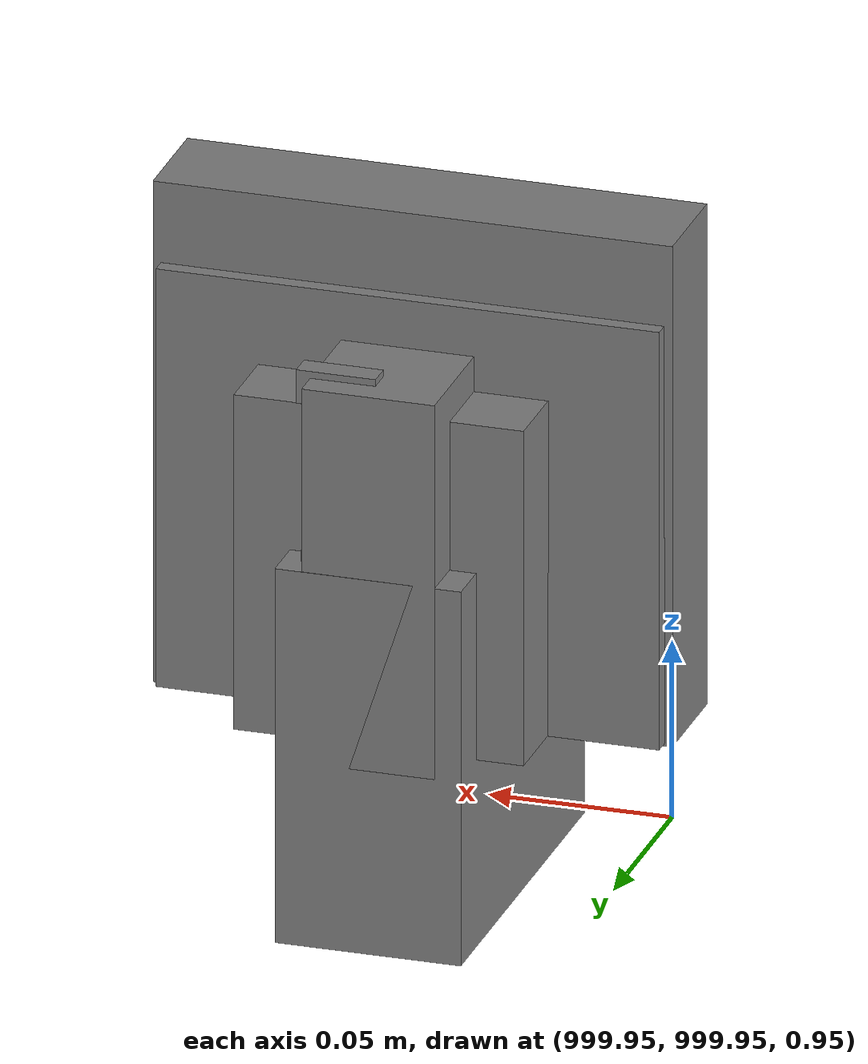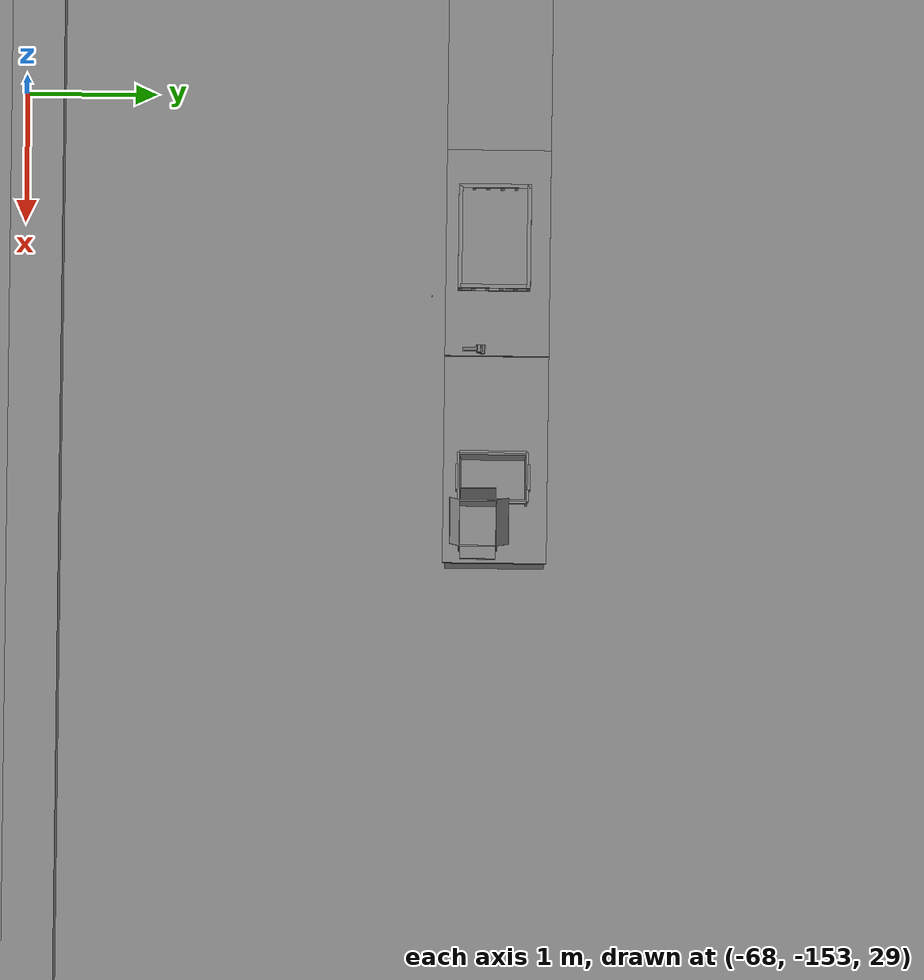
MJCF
<mujoco>
    <option gravity="0.000000000 0.000000000 -9.810000420" timestep="0.0049999999" integrator="implicitfast" density="1.225" viscosity="1.8000001e-05" noslip_iterations="10" iterations="100" sdf_iterations="50">
        <flag multiccd="disable"/>
    </option>
    <size memory="1000M"/>
    <compiler coordinate="local"/>
    <worldbody>
        <light cutoff="30" pos="0 1 1" dir="0 -1 -2"/>
        <light cutoff="30" pos="0 -1 1" dir="0 1 -2"/>
        <body pos="-66.377128601 -149.476898193 31.170850754" euler="-49.467655182 48.104785919 177.691986084" mocap="true" name="spotlight5_SpotLight"/>
        <body pos="1000.000000000 1000.000000000 1.000000000" euler="0.000000000 0.000000000 180.000000000" name="openloong_gripper_2f85_fix_base_usda_battery_01">
            <geom contype="1" conaffinity="1" density="1000" type="box" material="" rgba="0.500000000 0.500000000 0.500000000 1.000000000" solimp="0.899999976 0.949999988 0.001000000" friction="1.000000000 0.005000000 0.000100000" solref="0.020000000 1.000000000" margin="0" condim="3" group="0" pos="-0.011123657 -0.041940309 0.101691343" quat="1.000000000 0.000000000 0.000000000 0.000000000" size="0.010800000 0.003375000 0.004725000" name="openloong_gripper_2f85_fix_base_usda_geom_572614DD_8293_4730_BD35_67217A651467"/>
            <geom contype="1" conaffinity="1" density="1000" type="box" material="" rgba="0.500000000 0.500000000 0.500000000 1.000000000" solimp="0.899999976 0.949999988 0.001000000" friction="1.000000000 0.005000000 0.000100000" solref="0.020000000 1.000000000" margin="0" condim="3" group="0" pos="-0.010876465 -0.044247437 0.047066893" quat="0.998702705 -0.050920475 0.000000000 0.000000000" size="0.009450001 0.002700000 0.024975000" name="openloong_gripper_2f85_fix_base_usda_geom_D4B71727_8609_4CDB_9F9F_B715147E59EA"/>
            <geom contype="1" conaffinity="1" density="1000" type="box" material="" rgba="0.500000000 0.500000000 0.500000000 1.000000000" solimp="0.899999976 0.949999988 0.001000000" friction="1.000000000 0.005000000 0.000100000" solref="0.020000000 1.000000000" margin="0" condim="3" group="0" pos="-0.001235962 -0.000659180 0.047381196" quat="1.000000000 0.000000000 0.000000000 0.000000000" size="0.039420001 0.039150000 0.047250003" name="openloong_gripper_2f85_fix_base_usda_geom_0A9B032C_75A4_4520_9A4E_893AE9E5513E"/>
            <geom contype="1" conaffinity="1" density="1000" type="box" material="" rgba="0.500000000 0.500000000 0.500000000 1.000000000" solimp="0.899999976 0.949999988 0.001000000" friction="1.000000000 0.005000000 0.000100000" solref="0.020000000 1.000000000" margin="0" condim="3" group="0" pos="-0.010876465 -0.039138794 0.009851727" quat="1.000000000 0.000000000 0.000000000 0.000000000" size="0.009450001 0.010800000 0.013500000" name="openloong_gripper_2f85_fix_base_usda_geom_21224C98_DB54_4408_ABCE_C1D0C9673C84"/>
            <geom contype="1" conaffinity="1" density="1000" type="box" material="" rgba="0.500000000 0.500000000 0.500000000 1.000000000" solimp="0.899999976 0.949999988 0.001000000" friction="1.000000000 0.005000000 0.000100000" solref="0.020000000 1.000000000" margin="0" condim="3" group="0" pos="-0.010876465 -0.041528322 0.071508206" quat="1.000000000 0.000000000 0.000000000 0.000000000" size="0.009450001 0.002700000 0.027000001" name="openloong_gripper_2f85_fix_base_usda_geom_12AE39F4_F3F9_4CBF_BD01_1BAE2E9CE32C"/>
            <freejoint name="openloong_gripper_2f85_fix_base_usda_battery_01_joint"/>
            <site size="0.005000000 0.005000000 0.005000000" rgba="0.500000000 0.500000000 0.500000000 1.000000000" pos="0.000000000 0.000000000 0.000000000" quat="0.999961913 0.008726500 0.000000000 0.000000000" group="0" type="sphere" name="openloong_gripper_2f85_fix_base_usda_battery_01site"/>
        </body>
        <body pos="-65.859329224 -149.423385620 31.169115067" euler="-92.205039978 72.001434326 33.243240356" mocap="true" name="spotlight3_SpotLight"/>
        <body pos="1000.000000000 1000.000000000 1.000000000" euler="0.000000000 0.000000000 180.000000000" name="openloong_gripper_2f85_fix_base_usda_cpu_fan">
            <geom contype="1" conaffinity="1" density="1000" type="box" material="" rgba="0.500000000 0.500000000 0.500000000 1.000000000" solimp="0.899999976 0.949999988 0.001000000" friction="1.000000000 0.005000000 0.000100000" solref="0.020000000 1.000000000" margin="0" condim="3" group="0" pos="0.000000000 0.000000000 0.070034981" quat="0.000000000 0.000000000 0.000000000 1.000000000" size="0.070700005 0.014699999 0.070700005" name="openloong_gripper_2f85_fix_base_usda_geom_5999B337_B43E_468C_8098_628C3723EA19"/>
            <freejoint name="openloong_gripper_2f85_fix_base_usda_cpu_fan_joint"/>
            <site size="0.005000000 0.005000000 0.005000000" rgba="0.500000000 0.500000000 0.500000000 1.000000000" pos="0.000000000 0.000000000 0.000000000" quat="0.999961913 0.008726535 0.000000000 0.000000000" group="0" type="sphere" name="openloong_gripper_2f85_fix_base_usda_cpu_fancsite"/>
        </body>
        <body pos="1000.000000000 1000.000000000 1.000000000" euler="0.000000000 0.000000000 180.000000000" name="openloong_gripper_2f85_fix_base_usda_wifi_box">
            <geom contype="1" conaffinity="1" density="1000" type="box" material="" rgba="0.500000000 0.500000000 0.500000000 1.000000000" solimp="0.899999976 0.949999988 0.001000000" friction="1.000000000 0.005000000 0.000100000" solref="0.020000000 1.000000000" margin="0" condim="3" group="0" pos="0.000000000 0.000000000 0.058978677" quat="0.000000000 0.000000047 0.000000000 1.000000000" size="0.068499997 0.018999999 0.059000000" name="openloong_gripper_2f85_fix_base_usda_geom_44A44BC8_5F1D_43C4_BAF7_5FD9415E0CD4"/>
            <freejoint name="openloong_gripper_2f85_fix_base_usda_wifi_box_joint"/>
            <site size="0.005000000 0.005000000 0.005000000" rgba="0.500000000 0.500000000 0.500000000 1.000000000" pos="0.000000000 0.000000000 0.000000000" quat="0.999961913 0.008726500 0.000000000 0.000000000" group="0" type="sphere" name="openloong_gripper_2f85_fix_base_usda_wifi_boxsite"/>
        </body>
        <body pos="1000.000000000 1000.000000000 1.000000000" euler="0.000011953 0.000005123 -179.999984741" name="openloong_gripper_2f85_fix_base_usda_intel_box">
            <geom contype="1" conaffinity="1" density="1000" type="box" material="" rgba="0.500000000 0.500000000 0.500000000 1.000000000" solimp="0.899999976 0.949999988 0.001000000" friction="1.000000000 0.005000000 0.000100000" solref="0.020000000 1.000000000" margin="0" condim="3" group="0" pos="0.000000000 -0.000067139 0.000082284" quat="0.707106709 0.000000225 0.000000253 0.707106650" size="0.052800003 0.025300000 0.052800003" name="openloong_gripper_2f85_fix_base_usda_geom_AE3726FD_31D9_4531_B68B_7863F0F69ABB"/>
            <freejoint name="openloong_gripper_2f85_fix_base_usda_intel_box_joint"/>
            <site size="0.005000000 0.005000000 0.005000000" rgba="0.500000000 0.500000000 0.500000000 1.000000000" pos="0.000000000 0.000000000 0.000000000" quat="0.999961913 0.008726500 0.000000000 0.000000000" group="0" type="sphere" name="openloong_gripper_2f85_fix_base_usda_intel_boxsite"/>
        </body>
        <body pos="1000.000000000 999.999938965 1.000000000" euler="0.000000000 0.000000000 180.000000000" name="openloong_gripper_2f85_fix_base_usda_intelcore_i5">
            <geom contype="1" conaffinity="1" density="1000" type="box" material="" rgba="0.500000000 0.500000000 0.500000000 1.000000000" solimp="0.899999976 0.949999988 0.001000000" friction="1.000000000 0.005000000 0.000100000" solref="0.020000000 1.000000000" margin="0" condim="3" group="0" pos="0.000000000 0.000000000 0.051722717" quat="0.707106709 0.000000000 0.000000000 -0.707106769" size="0.052800000 0.018080002 0.052800000" name="openloong_gripper_2f85_fix_base_usda_geom_E6309AD2_39E2_442C_9E3C_C041ED1B50A9"/>
            <freejoint name="openloong_gripper_2f85_fix_base_usda_intelcore_i5_joint"/>
            <site size="0.005000000 0.005000000 0.005000000" rgba="0.500000000 0.500000000 0.500000000 1.000000000" pos="0.000000000 0.000000000 0.000000000" quat="0.999961913 0.008726534 0.000000000 0.000000000" group="0" type="sphere" name="openloong_gripper_2f85_fix_base_usda_intelcore_i5site"/>
        </body>
        <body pos="-65.801116943 -149.768981934 31.163494110" euler="168.819610596 -13.488757133 -75.690177917" mocap="true" name="spotlight1_SpotLight"/>
        <body pos="-64.866622925 -149.383972168 30.183746338" euler="89.999984741 89.999946594 0.000000000" name="openloong_gripper_2f85_fix_base_usda_bluebox_01">
            <geom contype="1" conaffinity="1" density="1000" type="box" material="" rgba="0.500000000 0.500000000 0.500000000 1.000000000" solimp="0.899999976 0.949999988 0.001000000" friction="1.000000000 0.005000000 0.000100000" solref="0.020000000 1.000000000" margin="0" condim="3" group="0" pos="0.276580811 0.187225342 0.000068665" quat="0.707106948 0.000077471 0.707106352 0.000077486" size="0.100000001 0.057999998 0.010000000" name="openloong_gripper_2f85_fix_base_usda_geom_61D69ED0_0E78_45DA_8BE1_15140B92B0B3"/>
            <geom contype="1" conaffinity="1" density="1000" type="box" material="" rgba="0.500000000 0.500000000 0.500000000 1.000000000" solimp="0.899999976 0.949999988 0.001000000" friction="1.000000000 0.005000000 0.000100000" solref="0.020000000 1.000000000" margin="0" condim="3" group="0" pos="0.000000000 0.002883911 0.000000000" quat="0.999999881 0.000000000 0.000000000 0.000000000" size="0.254000008 0.003000000 0.172000006" name="openloong_gripper_2f85_fix_base_usda_geom_98874061_BF13_4636_8775_FCA66F3D8C1D"/>
            <geom contype="1" conaffinity="1" density="1000" type="box" material="" rgba="0.500000000 0.500000000 0.500000000 1.000000000" solimp="0.899999976 0.949999988 0.001000000" friction="1.000000000 0.005000000 0.000100000" solref="0.020000000 1.000000000" margin="0" condim="3" group="0" pos="0.000000000 0.124874115 0.173484802" quat="0.999796331 0.020176515 -0.000000015 0.000000030" size="0.259999990 0.119999997 0.007000000" name="openloong_gripper_2f85_fix_base_usda_geom_A5E48D46_0784_4C00_B760_4D87A33223A5"/>
            <geom contype="1" conaffinity="1" density="1000" type="box" material="" rgba="0.500000000 0.500000000 0.500000000 1.000000000" solimp="0.899999976 0.949999988 0.001000000" friction="1.000000000 0.005000000 0.000100000" solref="0.020000000 1.000000000" margin="0" condim="3" group="0" pos="0.000000000 0.124874115 -0.173469543" quat="0.999796331 -0.020176545 -0.000000015 0.000000000" size="0.259999990 0.119999997 0.007000000" name="openloong_gripper_2f85_fix_base_usda_geom_AD2A7040_7501_4671_BEAE_45C28C7D76F8"/>
            <geom contype="1" conaffinity="1" density="1000" type="box" material="" rgba="0.500000000 0.500000000 0.500000000 1.000000000" solimp="0.899999976 0.949999988 0.001000000" friction="1.000000000 0.005000000 0.000100000" solref="0.020000000 1.000000000" margin="0" condim="3" group="0" pos="0.000000000 0.214008331 0.188980103" quat="0.999912977 0.013176724 0.000000015 0.000000000" size="0.259999990 0.029999999 0.012500000" name="openloong_gripper_2f85_fix_base_usda_geom_FBB298CF_211F_45EE_8842_8F130D8EC79A"/>
            <geom contype="1" conaffinity="1" density="1000" type="box" material="" rgba="0.500000000 0.500000000 0.500000000 1.000000000" solimp="0.899999976 0.949999988 0.001000000" friction="1.000000000 0.005000000 0.000100000" solref="0.020000000 1.000000000" margin="0" condim="3" group="0" pos="-0.258361816 0.125289917 0.001876831" quat="0.702796936 -0.020792112 0.710783124 0.020769298" size="0.189999998 0.119999997 0.009000000" name="openloong_gripper_2f85_fix_base_usda_geom_FCE8B808_4CE8_44D3_87A2_1447E6DB9A86"/>
            <geom contype="1" conaffinity="1" density="1000" type="box" material="" rgba="0.500000000 0.500000000 0.500000000 1.000000000" solimp="0.899999976 0.949999988 0.001000000" friction="1.000000000 0.005000000 0.000100000" solref="0.020000000 1.000000000" margin="0" condim="3" group="0" pos="0.000000000 0.214008331 -0.188980103" quat="0.999912977 -0.013176769 0.000000030 0.000000015" size="0.259999990 0.029999999 0.012500000" name="openloong_gripper_2f85_fix_base_usda_geom_827FB044_068B_4689_A820_A8EBBB0FE990"/>
            <geom contype="1" conaffinity="1" density="1000" type="box" material="" rgba="0.500000000 0.500000000 0.500000000 1.000000000" solimp="0.899999976 0.949999988 0.001000000" friction="1.000000000 0.005000000 0.000100000" solref="0.020000000 1.000000000" margin="0" condim="3" group="0" pos="-0.276611328 0.187225342 0.000068665" quat="0.707106650 0.000077441 0.707106709 0.000077456" size="0.100000001 0.057999998 0.010000000" name="openloong_gripper_2f85_fix_base_usda_geom_0A38E05C_8002_4A6B_80E5_BCCCFD664266"/>
            <geom contype="1" conaffinity="1" density="1000" type="box" material="" rgba="0.500000000 0.500000000 0.500000000 1.000000000" solimp="0.899999976 0.949999988 0.001000000" friction="1.000000000 0.005000000 0.000100000" solref="0.020000000 1.000000000" margin="0" condim="3" group="0" pos="0.258331299 0.125289917 0.001876831" quat="0.702851415 0.018856421 0.710823774 -0.019329369" size="0.189999998 0.119999997 0.009000000" name="openloong_gripper_2f85_fix_base_usda_geom_F3A0D011_04E8_4010_84FD_479DFDE21AAF"/>
            <freejoint name="openloong_gripper_2f85_fix_base_usda_bluebox_01_joint"/>
            <site size="0.005000000 0.005000000 0.005000000" rgba="0.500000000 0.500000000 0.500000000 1.000000000" pos="0.000000000 0.000000000 0.000000000" quat="0.999961913 0.008726534 0.000000000 0.000000000" group="0" type="sphere" name="openloong_gripper_2f85_fix_base_usda_bluebox_01site"/>
        </body>
        <body pos="-64.496299744 -149.491867065 30.235729218" euler="0.000000000 0.000000000 89.999946594" name="openloong_gripper_2f85_fix_base_usda_cardboardbox_01">
            <geom contype="1" conaffinity="1" density="1000" type="box" material="" rgba="0.500000000 0.500000000 0.500000000 1.000000000" solimp="0.899999976 0.949999988 0.001000000" friction="1.000000000 0.005000000 0.000100000" solref="0.020000000 1.000000000" margin="0" condim="3" group="0" pos="-0.003166199 -0.004086494 0.005052090" quat="1.000000000 0.000000000 0.000000000 0.000000000" size="0.142499998 0.177500010 0.005000000" name="openloong_gripper_2f85_fix_base_usda_geom_10746031_BFB2_44BA_9C19_DD279D2DDEE7"/>
            <geom contype="1" conaffinity="1" density="1000" type="box" material="" rgba="0.500000000 0.500000000 0.500000000 1.000000000" solimp="0.899999976 0.949999988 0.001000000" friction="1.000000000 0.005000000 0.000100000" solref="0.020000000 1.000000000" margin="0" condim="3" group="0" pos="-0.003166199 0.170316696 0.150570869" quat="1.000000000 0.000000000 0.000000000 0.000000000" size="0.142499998 0.005000000 0.149999991" name="openloong_gripper_2f85_fix_base_usda_geom_02AB3F60_3992_4BF8_B31D_99099E2D1123"/>
            <geom contype="1" conaffinity="1" density="1000" type="box" material="" rgba="0.500000000 0.500000000 0.500000000 1.000000000" solimp="0.899999976 0.949999988 0.001000000" friction="1.000000000 0.005000000 0.000100000" solref="0.020000000 1.000000000" margin="0" condim="3" group="0" pos="-0.147399902 -0.005307198 0.150570869" quat="1.000000000 0.000000000 0.000000000 0.000000000" size="0.005000000 0.177500010 0.149999991" name="openloong_gripper_2f85_fix_base_usda_geom_902D799F_18B3_49AB_8648_463CCD2E58C4"/>
            <geom contype="1" conaffinity="1" density="1000" type="box" material="" rgba="0.500000000 0.500000000 0.500000000 1.000000000" solimp="0.899999976 0.949999988 0.001000000" friction="1.000000000 0.005000000 0.000100000" solref="0.020000000 1.000000000" margin="0" condim="3" group="0" pos="0.140275955 -0.005307198 0.150570869" quat="1.000000000 0.000000000 0.000000000 0.000000000" size="0.005000000 0.177500010 0.149999991" name="openloong_gripper_2f85_fix_base_usda_geom_BD150FBF_5720_4413_95FF_017E420B1447"/>
            <geom contype="1" conaffinity="1" density="1000" type="box" material="" rgba="0.500000000 0.500000000 0.500000000 1.000000000" solimp="0.899999976 0.949999988 0.001000000" friction="1.000000000 0.005000000 0.000100000" solref="0.020000000 1.000000000" margin="0" condim="3" group="0" pos="-0.003166199 -0.181550980 0.150570869" quat="1.000000000 0.000000000 0.000000000 0.000000000" size="0.142499998 0.005000000 0.149999991" name="openloong_gripper_2f85_fix_base_usda_geom_A25762AE_F4C8_46EE_9460_11180CCAFB02"/>
            <freejoint name="openloong_gripper_2f85_fix_base_usda_cardboardbox_01_joint"/>
            <site size="0.005000000 0.005000000 0.005000000" rgba="0.500000000 0.500000000 0.500000000 1.000000000" pos="0.000000000 0.000000000 0.000000000" quat="0.999961913 0.008726535 0.000000000 0.000000000" group="0" type="sphere" name="openloong_gripper_2f85_fix_base_usda_site_E0A5A41D_28C4_4770_AD41_6C622FB299DF"/>
            <body pos="0.139160156 -0.004048347 0.301930904" euler="-179.999954224 49.383502960 179.999954224" name="openloong_gripper_2f85_fix_base_usda_A1_006">
                <geom contype="1" conaffinity="1" density="1000" type="box" material="" rgba="0.500000000 0.500000000 0.500000000 1.000000000" solimp="0.899999976 0.949999988 0.001000000" friction="1.000000000 0.005000000 0.000100000" solref="0.020000000 1.000000000" margin="0" condim="3" group="0" pos="-0.071587563 0.000009537 0.001745224" quat="0.999999881 0.000000000 0.000000000 0.000000000" size="0.071249999 0.179999992 0.002500000" name="openloong_gripper_2f85_fix_base_usda_geom_17AA13BA_243A_421A_9626_1FD782DBD7BD"/>
                <joint armature="0" stiffness="0.07" damping="0.0099999998" axis="0.000000 1.000000 0.000000" type="hinge" name="openloong_gripper_2f85_fix_base_usda_A1_006"/>
            </body>
            <body pos="-0.145902634 -0.004086494 0.301938057" euler="-180.000000000 -60.000011444 -180.000000000" name="openloong_gripper_2f85_fix_base_usda_A2_006">
                <geom contype="1" conaffinity="1" density="1000" type="box" material="" rgba="0.500000000 0.500000000 0.500000000 1.000000000" solimp="0.899999976 0.949999988 0.001000000" friction="1.000000000 0.005000000 0.000100000" solref="0.020000000 1.000000000" margin="0" condim="3" group="0" pos="0.071268082 0.000009537 0.002717972" quat="0.000002921 0.000000000 -0.000000030 0.999999881" size="0.071249999 0.179999992 0.002500000" name="openloong_gripper_2f85_fix_base_usda_geom_DE54B552_D623_4B5D_8C39_3F7335F8CFAC"/>
                <joint armature="0" stiffness="0.07" damping="0.0099999998" axis="0.000000 1.000000 0.000000" type="hinge" name="openloong_gripper_2f85_fix_base_usda_A2_006"/>
            </body>
            <body pos="-0.003385544 0.175991058 0.301930904" euler="-125.858116150 -0.000004561 0.000002331" name="openloong_gripper_2f85_fix_base_usda_B2_006">
                <geom contype="1" conaffinity="1" density="1000" type="box" material="" rgba="0.500000000 0.500000000 0.500000000 1.000000000" solimp="0.899999976 0.949999988 0.001000000" friction="1.000000000 0.005000000 0.000100000" solref="0.020000000 1.000000000" margin="0" condim="3" group="0" pos="0.000009537 -0.070939064 -0.002470016" quat="0.999614120 0.027776197 -0.000000015 0.000000030" size="0.137500003 0.064999998 0.005000000" name="openloong_gripper_2f85_fix_base_usda_geom_13ABFB84_A421_4C89_B5F0_584EAD63B88E"/>
                <joint armature="0" stiffness="0.07" damping="0.0099999998" axis="1.000000 0.000000 0.000000" type="hinge" name="openloong_gripper_2f85_fix_base_usda_B2_006"/>
            </body>
            <body pos="-0.003385544 -0.184140205 0.301938057" euler="147.805557251 0.000000000 0.000000000" name="openloong_gripper_2f85_fix_base_usda_B1_006">
                <geom contype="1" conaffinity="1" density="1000" type="box" material="" rgba="0.500000000 0.500000000 0.500000000 1.000000000" solimp="0.899999976 0.949999988 0.001000000" friction="1.000000000 0.005000000 0.000100000" solref="0.020000000 1.000000000" margin="0" condim="3" group="0" pos="-0.000028610 0.070202351 -0.002703667" quat="0.999614179 -0.027776167 0.000000000 0.000000000" size="0.137500003 0.064999998 0.005000000" name="openloong_gripper_2f85_fix_base_usda_geom_D9A538A2_6937_4830_91B2_3BB28EE567B2"/>
                <joint armature="0" stiffness="0.07" damping="0.0099999998" axis="1.000000 0.000000 0.000000" type="hinge" name="openloong_gripper_2f85_fix_base_usda_B1_006"/>
            </body>
        </body>
        <body pos="-65.882858276 -149.481979370 30.229999542" euler="-64.487716675 0.000000000 0.000000000" name="openloong_gripper_2f85_fix_base_usda_Barcode">
            <geom contype="1" conaffinity="1" density="1000" type="box" material="" rgba="0.500000000 0.500000000 0.500000000 1.000000000" solimp="0.899999976 0.949999988 0.001000000" friction="1.000000000 0.005000000 0.000100000" solref="0.020000000 1.000000000" margin="0" condim="3" group="0" pos="0.000000000 0.013038635 0.001419067" quat="0.000000000 0.000000000 0.000000000 1.000000119" size="0.034000002 0.010000000 0.017999999" name="openloong_gripper_2f85_fix_base_usda_geom_7A193786_631D_45B7_980B_9D2F73001995"/>
            <geom contype="1" conaffinity="1" density="1000" type="box" material="" rgba="0.500000000 0.500000000 0.500000000 1.000000000" solimp="0.899999976 0.949999988 0.001000000" friction="1.000000000 0.005000000 0.000100000" solref="0.020000000 1.000000000" margin="0" condim="3" group="0" pos="0.000000000 -0.035301208 -0.007095337" quat="0.000000000 0.000000000 -0.043619365 0.999048233" size="0.028999999 0.010000000 0.020000000" name="openloong_gripper_2f85_fix_base_usda_geom_6149DE2E_D410_4601_900C_B08BB4AE178B"/>
            <geom contype="1" conaffinity="1" density="1000" type="box" material="" rgba="0.500000000 0.500000000 0.500000000 1.000000000" solimp="0.899999976 0.949999988 0.001000000" friction="1.000000000 0.005000000 0.000100000" solref="0.020000000 1.000000000" margin="0" condim="3" group="0" pos="0.000000000 -0.043411255 -0.011749268" quat="0.922262907 0.386563420 0.000000000 0.000000000" size="0.026000001 0.010000000 0.020000000" name="openloong_gripper_2f85_fix_base_usda_geom_37B43CCF_2563_4AFA_A3CF_7A1E2A75104D"/>
            <geom contype="1" conaffinity="1" density="1000" type="box" material="" rgba="0.500000000 0.500000000 0.500000000 1.000000000" solimp="0.899999976 0.949999988 0.001000000" friction="1.000000000 0.005000000 0.000100000" solref="0.020000000 1.000000000" margin="0" condim="3" group="0" pos="0.000000000 -0.016967773 -0.031860352" quat="0.000000000 0.000000000 0.000000000 1.000000119" size="0.008000000 0.010000000 0.013000000" name="openloong_gripper_2f85_fix_base_usda_geom_0EA476B3_1D1E_40E0_A7BB_449782518623"/>
            <geom contype="1" conaffinity="1" density="1000" type="box" material="" rgba="0.500000000 0.500000000 0.500000000 1.000000000" solimp="0.899999976 0.949999988 0.001000000" friction="1.000000000 0.005000000 0.000100000" solref="0.020000000 1.000000000" margin="0" condim="3" group="0" pos="0.000000000 -0.001869202 0.000312805" quat="0.953716993 0.300705761 0.000000000 0.000000000" size="0.032000002 0.010000000 0.018999999" name="openloong_gripper_2f85_fix_base_usda_geom_09F6088E_EFD9_4D7D_A202_E9FAF03B2A4D"/>
            <geom contype="1" conaffinity="1" density="1000" type="box" material="" rgba="0.500000000 0.500000000 0.500000000 1.000000000" solimp="0.899999976 0.949999988 0.001000000" friction="1.000000000 0.005000000 0.000100000" solref="0.020000000 1.000000000" margin="0" condim="3" group="0" pos="0.000000000 -0.019531250 -0.003173828" quat="0.953716993 0.300705761 0.000000000 0.000000000" size="0.030999999 0.010000000 0.020000000" name="openloong_gripper_2f85_fix_base_usda_geom_AECA15B7_87E7_49B2_A3B3_6AE09AC730A8"/>
            <geom contype="1" conaffinity="1" density="1000" type="box" material="" rgba="0.500000000 0.500000000 0.500000000 1.000000000" solimp="0.899999976 0.949999988 0.001000000" friction="1.000000000 0.005000000 0.000100000" solref="0.020000000 1.000000000" margin="0" condim="3" group="0" pos="0.000000000 -0.035301208 -0.007095337" quat="0.953716993 0.300705761 0.000000000 0.000000000" size="0.028999999 0.010000000 0.020000000" name="openloong_gripper_2f85_fix_base_usda_geom_8ED1C093_2083_4742_9F86_95E496EB9AA0"/>
            <geom contype="1" conaffinity="1" density="1000" type="box" material="" rgba="0.500000000 0.500000000 0.500000000 1.000000000" solimp="0.899999976 0.949999988 0.001000000" friction="1.000000000 0.005000000 0.000100000" solref="0.020000000 1.000000000" margin="0" condim="3" group="0" pos="0.000000000 -0.042617798 -0.071121216" quat="0.000000000 0.000000000 0.000000000 1.000000119" size="0.013000000 0.021000000 0.059999999" name="openloong_gripper_2f85_fix_base_usda_geom_833B1594_5417_4ACD_82FC_3154A659E2C3"/>
            <freejoint name="openloong_gripper_2f85_fix_base_usda_Barcode_joint"/>
            <site size="0.005000000 0.005000000 0.005000000" rgba="0.500000000 0.500000000 0.500000000 1.000000000" pos="0.000000000 0.000000000 0.000000000" quat="1.000000000 0.000000000 0.000000000 0.000000000" group="0" type="sphere" name="openloong_gripper_2f85_fix_base_usda_Barcode_site"/>
        </body>
        <body pos="-66.745018005 -149.392349243 30.184000015" euler="0.000000000 0.000000000 89.999946594" name="[22332165846851]_Basket_01">
            <geom contype="1" conaffinity="1" density="1000" type="box" material="" rgba="0.500000000 0.500000000 0.500000000 1.000000000" solimp="0.899999976 0.949999988 0.001000000" friction="1.000000000 0.005000000 0.000100000" solref="0.020000000 1.000000000" margin="0" condim="3" group="0" pos="-0.052425385 0.389207840 0.089787483" quat="0.707107008 0.000000000 0.000000000 0.707106411" size="0.014249999 0.014249999 0.059999999" name="[22332165846851]_geom_CEC8B4EA_DDB4_4BCE_9FF5_D2E65C8469C7"/>
            <geom contype="1" conaffinity="1" density="1000" type="box" material="" rgba="0.500000000 0.500000000 0.500000000 1.000000000" solimp="0.899999976 0.949999988 0.001000000" friction="1.000000000 0.005000000 0.000100000" solref="0.020000000 1.000000000" margin="0" condim="3" group="0" pos="0.264015198 -0.133043289 0.089787483" quat="0.707107008 0.000000000 0.000000000 0.707106411" size="0.014249999 0.014249999 0.059999999" name="[22332165846851]_geom_F19AB43D_EDA8_430F_8A54_07BF73142400"/>
            <geom contype="1" conaffinity="1" density="1000" type="box" material="" rgba="0.500000000 0.500000000 0.500000000 1.000000000" solimp="0.899999976 0.949999988 0.001000000" friction="1.000000000 0.005000000 0.000100000" solref="0.020000000 1.000000000" margin="0" condim="3" group="0" pos="-0.264015198 -0.265548706 0.089793205" quat="0.707107008 0.000000000 0.000000000 0.707106411" size="0.014249999 0.014249999 0.059999999" name="[22332165846851]_geom_E3640891_C7DE_468A_BE6C_69A7075E4285"/>
            <geom contype="1" conaffinity="1" density="1000" type="box" material="" rgba="0.500000000 0.500000000 0.500000000 1.000000000" solimp="0.899999976 0.949999988 0.001000000" friction="1.000000000 0.005000000 0.000100000" solref="0.020000000 1.000000000" margin="0" condim="3" group="0" pos="-0.160263062 -0.389322281 0.089793205" quat="0.707107008 0.000000000 0.000000000 0.707106411" size="0.014249999 0.014249999 0.059999999" name="[22332165846851]_geom_10C1C4C7_749E_4444_BC3F_3E96570354AD"/>
            <geom contype="1" conaffinity="1" density="1000" type="box" material="" rgba="0.500000000 0.500000000 0.500000000 1.000000000" solimp="0.899999976 0.949999988 0.001000000" friction="1.000000000 0.005000000 0.000100000" solref="0.020000000 1.000000000" margin="0" condim="3" group="0" pos="0.162265778 -0.389322281 0.089787483" quat="0.707107008 0.000000000 0.000000000 0.707106411" size="0.014249999 0.014249999 0.059999999" name="[22332165846851]_geom_8A0ACD88_2E45_4198_BDDE_02216A697B59"/>
            <geom contype="1" conaffinity="1" density="1000" type="box" material="" rgba="0.500000000 0.500000000 0.500000000 1.000000000" solimp="0.899999976 0.949999988 0.001000000" friction="1.000000000 0.005000000 0.000100000" solref="0.020000000 1.000000000" margin="0" condim="3" group="0" pos="0.264015198 0.389207840 0.089787483" quat="0.707107008 0.000000000 0.000000000 0.707106411" size="0.014249999 0.014249999 0.059999999" name="[22332165846851]_geom_678FDE8C_3F05_4FFE_A6B1_132493F13CAA"/>
            <geom contype="1" conaffinity="1" density="1000" type="box" material="" rgba="0.500000000 0.500000000 0.500000000 1.000000000" solimp="0.899999976 0.949999988 0.001000000" friction="1.000000000 0.005000000 0.000100000" solref="0.020000000 1.000000000" margin="0" condim="3" group="0" pos="-0.264015198 -0.133043289 0.089793205" quat="0.707107008 0.000000000 0.000000000 0.707106411" size="0.014249999 0.014249999 0.059999999" name="[22332165846851]_geom_8CA9B197_A968_45F1_8905_6BDC92B103E7"/>
            <geom contype="1" conaffinity="1" density="1000" type="box" material="" rgba="0.500000000 0.500000000 0.500000000 1.000000000" solimp="0.899999976 0.949999988 0.001000000" friction="1.000000000 0.005000000 0.000100000" solref="0.020000000 1.000000000" margin="0" condim="3" group="0" pos="-0.264026642 0.269256592 0.089793205" quat="0.707107008 0.000000000 0.000000000 0.707106411" size="0.014249999 0.014249999 0.059999999" name="[22332165846851]_geom_42220AB0_8A4B_45A3_8901_1849AB4F321E"/>
            <geom contype="1" conaffinity="1" density="1000" type="box" material="" rgba="0.500000000 0.500000000 0.500000000 1.000000000" solimp="0.899999976 0.949999988 0.001000000" friction="1.000000000 0.005000000 0.000100000" solref="0.020000000 1.000000000" margin="0" condim="3" group="0" pos="0.054462433 0.389207840 0.089787483" quat="0.707107008 0.000000000 0.000000000 0.707106411" size="0.014249999 0.014249999 0.059999999" name="[22332165846851]_geom_642CEA6C_5E8B_49F0_955C_07E17AEB1F84"/>
            <geom contype="1" conaffinity="1" density="1000" type="box" material="" rgba="0.500000000 0.500000000 0.500000000 1.000000000" solimp="0.899999976 0.949999988 0.001000000" friction="1.000000000 0.005000000 0.000100000" solref="0.020000000 1.000000000" margin="0" condim="3" group="0" pos="0.054462433 -0.389322281 0.089787483" quat="0.707107008 0.000000000 0.000000000 0.707106411" size="0.014249999 0.014249999 0.059999999" name="[22332165846851]_geom_C3609B5B_8015_4FDA_87A5_89193E99ECBD"/>
            <geom contype="1" conaffinity="1" density="1000" type="box" material="" rgba="0.500000000 0.500000000 0.500000000 1.000000000" solimp="0.899999976 0.949999988 0.001000000" friction="1.000000000 0.005000000 0.000100000" solref="0.020000000 1.000000000" margin="0" condim="3" group="0" pos="0.264015198 0.269256592 0.089793205" quat="0.707107008 0.000000000 0.000000000 0.707106411" size="0.014249999 0.014249999 0.059999999" name="[22332165846851]_geom_01D19344_AEF7_4E61_ACC1_3FBD69302213"/>
            <geom contype="1" conaffinity="1" density="1000" type="box" material="" rgba="0.500000000 0.500000000 0.500000000 1.000000000" solimp="0.899999976 0.949999988 0.001000000" friction="1.000000000 0.005000000 0.000100000" solref="0.020000000 1.000000000" margin="0" condim="3" group="0" pos="0.264015198 -0.389322281 0.089787483" quat="0.707107008 0.000000000 0.000000000 0.707106411" size="0.014249999 0.014249999 0.059999999" name="[22332165846851]_geom_F63E7137_DF35_496E_AC37_0EA8CFDEC0A1"/>
            <geom contype="1" conaffinity="1" density="1000" type="box" material="" rgba="0.500000000 0.500000000 0.500000000 1.000000000" solimp="0.899999976 0.949999988 0.001000000" friction="1.000000000 0.005000000 0.000100000" solref="0.020000000 1.000000000" margin="0" condim="3" group="0" pos="0.000000000 0.000000000 0.015998840" quat="0.707107008 0.000000000 0.000000000 0.707106411" size="0.403499991 0.279000014 0.015750000" name="[22332165846851]_geom_CC845982_665C_4005_A390_91F300899ECE"/>
            <geom contype="1" conaffinity="1" density="1000" type="box" material="" rgba="0.500000000 0.500000000 0.500000000 1.000000000" solimp="0.899999976 0.949999988 0.001000000" friction="1.000000000 0.005000000 0.000100000" solref="0.020000000 1.000000000" margin="0" condim="3" group="0" pos="0.000000000 -0.389476776 0.163619041" quat="0.707107008 0.000000000 0.000000000 0.707106411" size="0.015000000 0.277500004 0.015750000" name="[22332165846851]_geom_E6E1A831_CABA_49C8_97DC_751F201F150F"/>
            <geom contype="1" conaffinity="1" density="1000" type="box" material="" rgba="0.500000000 0.500000000 0.500000000 1.000000000" solimp="0.899999976 0.949999988 0.001000000" friction="1.000000000 0.005000000 0.000100000" solref="0.020000000 1.000000000" margin="0" condim="3" group="0" pos="0.162265778 0.389207840 0.089787483" quat="0.707107008 0.000000000 0.000000000 0.707106411" size="0.014249999 0.014249999 0.059999999" name="[22332165846851]_geom_E745D97F_EE68_448D_9D6D_C5EFB549CC6A"/>
            <geom contype="1" conaffinity="1" density="1000" type="box" material="" rgba="0.500000000 0.500000000 0.500000000 1.000000000" solimp="0.899999976 0.949999988 0.001000000" friction="1.000000000 0.005000000 0.000100000" solref="0.020000000 1.000000000" margin="0" condim="3" group="0" pos="0.000000000 0.389471054 0.163619041" quat="0.707107008 0.000000000 0.000000000 0.707106411" size="0.015000000 0.277500004 0.015750000" name="[22332165846851]_geom_4F1EB3D8_6BD2_4611_A53D_67478913902A"/>
            <geom contype="1" conaffinity="1" density="1000" type="box" material="" rgba="0.500000000 0.500000000 0.500000000 1.000000000" solimp="0.899999976 0.949999988 0.001000000" friction="1.000000000 0.005000000 0.000100000" solref="0.020000000 1.000000000" margin="0" condim="3" group="0" pos="-0.263511658 0.000000000 0.163619041" quat="0.707107008 0.000000000 0.000000000 0.707106411" size="0.403499991 0.015000000 0.015750000" name="[22332165846851]_geom_5E22CA54_A962_405D_BAA6_E3E5EF4E84D1"/>
            <geom contype="1" conaffinity="1" density="1000" type="box" material="" rgba="0.500000000 0.500000000 0.500000000 1.000000000" solimp="0.899999976 0.949999988 0.001000000" friction="1.000000000 0.005000000 0.000100000" solref="0.020000000 1.000000000" margin="0" condim="3" group="0" pos="-0.264015198 0.141334534 0.089793205" quat="0.707107008 0.000000000 0.000000000 0.707106411" size="0.014249999 0.014249999 0.059999999" name="[22332165846851]_geom_C1F7CA70_05C3_415E_9144_098F18B8445D"/>
            <geom contype="1" conaffinity="1" density="1000" type="box" material="" rgba="0.500000000 0.500000000 0.500000000 1.000000000" solimp="0.899999976 0.949999988 0.001000000" friction="1.000000000 0.005000000 0.000100000" solref="0.020000000 1.000000000" margin="0" condim="3" group="0" pos="0.264015198 -0.265548706 0.089787483" quat="0.707107008 0.000000000 0.000000000 0.707106411" size="0.014249999 0.014249999 0.059999999" name="[22332165846851]_geom_4E902418_2249_4F4C_AFFB_4EFE1C675724"/>
            <geom contype="1" conaffinity="1" density="1000" type="box" material="" rgba="0.500000000 0.500000000 0.500000000 1.000000000" solimp="0.899999976 0.949999988 0.001000000" friction="1.000000000 0.005000000 0.000100000" solref="0.020000000 1.000000000" margin="0" condim="3" group="0" pos="-0.160263062 0.389207840 0.089787483" quat="0.707107008 0.000000000 0.000000000 0.707106411" size="0.014249999 0.014249999 0.059999999" name="[22332165846851]_geom_893C12EF_CF6C_44B5_97CA_29B1E88FDE58"/>
            <geom contype="1" conaffinity="1" density="1000" type="box" material="" rgba="0.500000000 0.500000000 0.500000000 1.000000000" solimp="0.899999976 0.949999988 0.001000000" friction="1.000000000 0.005000000 0.000100000" solref="0.020000000 1.000000000" margin="0" condim="3" group="0" pos="-0.052425385 -0.389322281 0.089787483" quat="0.707107008 0.000000000 0.000000000 0.707106411" size="0.014249999 0.014249999 0.059999999" name="[22332165846851]_geom_601898EC_CFC7_403D_BCAA_70E8A65DA9B3"/>
            <geom contype="1" conaffinity="1" density="1000" type="box" material="" rgba="0.500000000 0.500000000 0.500000000 1.000000000" solimp="0.899999976 0.949999988 0.001000000" friction="1.000000000 0.005000000 0.000100000" solref="0.020000000 1.000000000" margin="0" condim="3" group="0" pos="-0.264026642 -0.389322281 0.089793205" quat="0.707107008 0.000000000 0.000000000 0.707106411" size="0.014249999 0.014249999 0.059999999" name="[22332165846851]_geom_E852326E_AD61_4250_A956_F52A507AC84B"/>
            <geom contype="1" conaffinity="1" density="1000" type="box" material="" rgba="0.500000000 0.500000000 0.500000000 1.000000000" solimp="0.899999976 0.949999988 0.001000000" friction="1.000000000 0.005000000 0.000100000" solref="0.020000000 1.000000000" margin="0" condim="3" group="0" pos="0.264015198 0.141334534 0.089787483" quat="0.707107008 0.000000000 0.000000000 0.707106411" size="0.014249999 0.014249999 0.059999999" name="[22332165846851]_geom_5C68E509_D859_46BB_9792_80F9B0FC586B"/>
            <geom contype="1" conaffinity="1" density="1000" type="box" material="" rgba="0.500000000 0.500000000 0.500000000 1.000000000" solimp="0.899999976 0.949999988 0.001000000" friction="1.000000000 0.005000000 0.000100000" solref="0.020000000 1.000000000" margin="0" condim="3" group="0" pos="-0.264015198 0.389207840 0.089793205" quat="0.707107008 0.000000000 0.000000000 0.707106411" size="0.014249999 0.014249999 0.059999999" name="[22332165846851]_geom_EF074554_3767_413D_8BC8_5144AB771A68"/>
            <geom contype="1" conaffinity="1" density="1000" type="box" material="" rgba="0.500000000 0.500000000 0.500000000 1.000000000" solimp="0.899999976 0.949999988 0.001000000" friction="1.000000000 0.005000000 0.000100000" solref="0.020000000 1.000000000" margin="0" condim="3" group="0" pos="0.264015198 0.004480362 0.089787483" quat="0.707107008 0.000000000 0.000000000 0.707106411" size="0.014249999 0.014249999 0.059999999" name="[22332165846851]_geom_7F386371_47AE_46E8_A4B5_1F15D001E1C0"/>
            <geom contype="1" conaffinity="1" density="1000" type="box" material="" rgba="0.500000000 0.500000000 0.500000000 1.000000000" solimp="0.899999976 0.949999988 0.001000000" friction="1.000000000 0.005000000 0.000100000" solref="0.020000000 1.000000000" margin="0" condim="3" group="0" pos="0.263694763 -0.000011444 0.163619041" quat="0.707107008 0.000000000 0.000000000 0.707106411" size="0.403499991 0.015000000 0.015750000" name="[22332165846851]_geom_C044A65A_4305_4F69_9630_C6296C987D42"/>
            <geom contype="1" conaffinity="1" density="1000" type="box" material="" rgba="0.500000000 0.500000000 0.500000000 1.000000000" solimp="0.899999976 0.949999988 0.001000000" friction="1.000000000 0.005000000 0.000100000" solref="0.020000000 1.000000000" margin="0" condim="3" group="0" pos="-0.264015198 0.004480362 0.089793205" quat="0.707107008 0.000000000 0.000000000 0.707106411" size="0.014249999 0.014249999 0.059999999" name="[22332165846851]_geom_F2BFE8D1_FB70_4CEC_918B_922ECD3334F5"/>
            <freejoint name="[22332165846851]_joint_BC4C731D_8CD9_450C_A33D_1D3E33C0A0A9"/>
        </body>
        <body pos="0.000000000 0.000000000 0.000000000" euler="0.000000000 0.000000000 0.000000000" name="Static Objects_Static Objects">
            <geom contype="1" conaffinity="1" density="1000" type="box" material="" rgba="0.500000000 0.500000000 0.500000000 1.000000000" solimp="0.899999976 0.949999988 0.001000000" friction="1.000000000 0.005000000 0.000100000" solref="0.020000000 1.000000000" margin="0" condim="3" group="0" pos="-67.544113159 -149.365814209 29.727830887" quat="0.500000417 0.499999970 0.499999553 0.499999970" size="0.381000012 0.319999993 0.041000001" name="Static Objects_geom_95EC3334_534B_4D00_8941_223BEB288586"/>
            <geom contype="1" conaffinity="1" density="1000" type="box" material="" rgba="0.500000000 0.500000000 0.500000000 1.000000000" solimp="0.899999976 0.949999988 0.001000000" friction="1.000000000 0.005000000 0.000100000" solref="0.020000000 1.000000000" margin="0" condim="3" group="0" pos="-68.239501953 -149.365814209 30.086868286" quat="0.500000417 0.499999970 0.499999553 0.499999970" size="0.370999992 0.039500002 0.745000005" name="Static Objects_geom_BD50DE07_0BF9_4A46_9D84_8E185B9363EB"/>
            <geom contype="1" conaffinity="1" density="1000" type="box" material="" rgba="0.500000000 0.500000000 0.500000000 1.000000000" solimp="0.899999976 0.949999988 0.001000000" friction="1.000000000 0.005000000 0.000100000" solref="0.020000000 1.000000000" margin="0" condim="3" group="0" pos="-68.239501953 -149.365814209 30.147235870" quat="0.500000417 0.499999970 0.499999553 0.499999970" size="0.400000006 0.022000000 0.800000012" name="Static Objects_geom_CE157A96_E9B7_47FE_8B34_23C6872E79CB"/>
            <geom contype="1" conaffinity="1" density="1000" type="box" material="" rgba="0.500000000 0.500000000 0.500000000 1.000000000" solimp="0.899999976 0.949999988 0.001000000" friction="1.000000000 0.005000000 0.000100000" solref="0.020000000 1.000000000" margin="0" condim="3" group="0" pos="-68.934890747 -149.365814209 29.727830887" quat="0.500000417 0.499999970 0.499999553 0.499999970" size="0.381000012 0.319999993 0.041000001" name="Static Objects_geom_5FC3E84C_CACC_4CD7_9E75_94452E36D814"/>
            <geom contype="1" conaffinity="1" density="1000" type="box" material="" rgba="0.500000000 0.500000000 0.500000000 1.000000000" solimp="0.899999976 0.949999988 0.001000000" friction="1.000000000 0.005000000 0.000100000" solref="0.020000000 1.000000000" margin="0" condim="3" group="0" pos="-68.239501953 -149.365814209 29.561563492" quat="0.500000417 0.499999970 0.499999553 0.499999970" size="0.020000000 0.022000000 0.660000026" name="Static Objects_geom_37FA2C64_6F0B_41FC_B225_5BBE2F053B9C"/>
            <geom contype="1" conaffinity="1" density="1000" type="box" material="" rgba="0.500000000 0.500000000 0.500000000 1.000000000" solimp="0.899999976 0.949999988 0.001000000" friction="1.000000000 0.005000000 0.000100000" solref="0.020000000 1.000000000" margin="0" condim="3" group="0" pos="-65.945671082 -149.365814209 29.727830887" quat="0.500000417 0.499999970 0.499999553 0.499999970" size="0.381000012 0.319999993 0.041000001" name="Static Objects_geom_F6559F5F_7ADA_4553_A2D2_26E8ADABA0DC"/>
            <geom contype="1" conaffinity="1" density="1000" type="box" material="" rgba="0.500000000 0.500000000 0.500000000 1.000000000" solimp="0.899999976 0.949999988 0.001000000" friction="1.000000000 0.005000000 0.000100000" solref="0.020000000 1.000000000" margin="0" condim="3" group="0" pos="-66.641059875 -149.365814209 30.086868286" quat="0.500000417 0.499999970 0.499999553 0.499999970" size="0.370999992 0.039500002 0.745000005" name="Static Objects_geom_CE90C296_A882_43FE_85BB_1869A3A9E600"/>
            <geom contype="1" conaffinity="1" density="1000" type="box" material="" rgba="0.500000000 0.500000000 0.500000000 1.000000000" solimp="0.899999976 0.949999988 0.001000000" friction="1.000000000 0.005000000 0.000100000" solref="0.020000000 1.000000000" margin="0" condim="3" group="0" pos="-66.641059875 -149.365814209 30.147235870" quat="0.500000417 0.499999970 0.499999553 0.499999970" size="0.400000006 0.022000000 0.800000012" name="Static Objects_geom_4CA87343_475D_4433_A465_79A3AA21EEFB"/>
            <geom contype="1" conaffinity="1" density="1000" type="box" material="" rgba="0.500000000 0.500000000 0.500000000 1.000000000" solimp="0.899999976 0.949999988 0.001000000" friction="1.000000000 0.005000000 0.000100000" solref="0.020000000 1.000000000" margin="0" condim="3" group="0" pos="-67.336448669 -149.365814209 29.727830887" quat="0.500000417 0.499999970 0.499999553 0.499999970" size="0.381000012 0.319999993 0.041000001" name="Static Objects_geom_7F6F31AB_11B4_4AEB_B91A_AA24C72C3603"/>
            <geom contype="1" conaffinity="1" density="1000" type="box" material="" rgba="0.500000000 0.500000000 0.500000000 1.000000000" solimp="0.899999976 0.949999988 0.001000000" friction="1.000000000 0.005000000 0.000100000" solref="0.020000000 1.000000000" margin="0" condim="3" group="0" pos="-66.641059875 -149.365814209 29.561563492" quat="0.500000417 0.499999970 0.499999553 0.499999970" size="0.020000000 0.022000000 0.660000026" name="Static Objects_geom_3A1CC329_4304_4C85_8BE2_87044A80C3D7"/>
            <geom contype="1" conaffinity="1" density="1000" type="box" material="" rgba="0.500000000 0.500000000 0.500000000 1.000000000" solimp="0.899999976 0.949999988 0.001000000" friction="1.000000000 0.005000000 0.000100000" solref="0.020000000 1.000000000" margin="0" condim="3" group="0" pos="-64.338577271 -149.365814209 29.727830887" quat="0.500000417 0.499999970 0.499999553 0.499999970" size="0.381000012 0.319999993 0.041000001" name="Static Objects_geom_107BB721_A94D_43F1_AE93_B59A3918B964"/>
            <geom contype="1" conaffinity="1" density="1000" type="box" material="" rgba="0.500000000 0.500000000 0.500000000 1.000000000" solimp="0.899999976 0.949999988 0.001000000" friction="1.000000000 0.005000000 0.000100000" solref="0.020000000 1.000000000" margin="0" condim="3" group="0" pos="-65.033966064 -149.365814209 30.086868286" quat="0.500000417 0.499999970 0.499999553 0.499999970" size="0.370999992 0.039500002 0.745000005" name="Static Objects_geom_C1BAF8E7_0474_469D_A409_9537D9AB9456"/>
            <geom contype="1" conaffinity="1" density="1000" type="box" material="" rgba="0.500000000 0.500000000 0.500000000 1.000000000" solimp="0.899999976 0.949999988 0.001000000" friction="1.000000000 0.005000000 0.000100000" solref="0.020000000 1.000000000" margin="0" condim="3" group="0" pos="-65.033966064 -149.365814209 30.147235870" quat="0.500000417 0.499999970 0.499999553 0.499999970" size="0.400000006 0.022000000 0.800000012" name="Static Objects_geom_F6C8A91E_8BDA_46CB_9772_B8C6FE69905F"/>
            <geom contype="1" conaffinity="1" density="1000" type="box" material="" rgba="0.500000000 0.500000000 0.500000000 1.000000000" solimp="0.899999976 0.949999988 0.001000000" friction="1.000000000 0.005000000 0.000100000" solref="0.020000000 1.000000000" margin="0" condim="3" group="0" pos="-65.729354858 -149.365814209 29.727830887" quat="0.500000417 0.499999970 0.499999553 0.499999970" size="0.381000012 0.319999993 0.041000001" name="Static Objects_geom_B141CAB5_809E_4456_807D_01D83E7145E2"/>
            <geom contype="1" conaffinity="1" density="1000" type="box" material="" rgba="0.500000000 0.500000000 0.500000000 1.000000000" solimp="0.899999976 0.949999988 0.001000000" friction="1.000000000 0.005000000 0.000100000" solref="0.020000000 1.000000000" margin="0" condim="3" group="0" pos="-65.033966064 -149.365814209 29.561563492" quat="0.500000417 0.499999970 0.499999553 0.499999970" size="0.020000000 0.022000000 0.660000026" name="Static Objects_geom_FF82D62D_7541_46FE_8293_A620267FDA88"/>
            <geom contype="1" conaffinity="1" density="1000" type="box" material="" rgba="0.500000000 0.500000000 0.500000000 1.000000000" solimp="0.899999976 0.949999988 0.001000000" friction="1.000000000 0.005000000 0.000100000" solref="0.020000000 1.000000000" margin="0" condim="3" group="0" pos="-61.754566193 -137.853729248 33.906845093" quat="0.707107067 0.000000000 0.000000000 0.707106471" size="0.759999990 0.759999990 4.500000000" name="Static Objects_geom_08B00ADE_B07D_451C_BBD0_32AEB38A51F8"/>
            <geom contype="1" conaffinity="1" density="1000" type="box" material="" rgba="0.500000000 0.500000000 0.500000000 1.000000000" solimp="0.899999976 0.949999988 0.001000000" friction="1.000000000 0.005000000 0.000100000" solref="0.020000000 1.000000000" margin="0" condim="3" group="0" pos="-57.511135101 -144.927108765 31.707921982" quat="1.000000000 0.000000000 0.000000000 0.000000000" size="0.200000003 8.000000000 2.299999952" name="Static Objects_geom_3D9F7201_28D3_4331_BB78_A74AA23EC7B0"/>
            <geom contype="1" conaffinity="1" density="1000" type="box" material="" rgba="0.500000000 0.500000000 0.500000000 1.000000000" solimp="0.899999976 0.949999988 0.001000000" friction="1.000000000 0.005000000 0.000100000" solref="0.020000000 1.000000000" margin="0" condim="3" group="0" pos="-80.517646790 -157.574050903 31.688196182" quat="0.707107067 0.000000000 0.000000000 0.707106471" size="0.600000024 0.600000024 2.299999952" name="Static Objects_geom_2A31B3BB_16CE_45D9_AC54_8ACD8DE81631"/>
            <geom contype="1" conaffinity="1" density="1000" type="box" material="" rgba="0.500000000 0.500000000 0.500000000 1.000000000" solimp="0.899999976 0.949999988 0.001000000" friction="1.000000000 0.005000000 0.000100000" solref="0.020000000 1.000000000" margin="0" condim="3" group="0" pos="-80.711044312 -147.414932251 31.666158676" quat="1.000000000 0.000000000 0.000000000 0.000000000" size="0.200000003 10.000000000 2.299999952" name="Static Objects_geom_09C65FA1_DBB4_4850_8082_C932C6219C7E"/>
            <geom contype="1" conaffinity="1" density="1000" type="box" material="" rgba="0.500000000 0.500000000 0.500000000 1.000000000" solimp="0.899999976 0.949999988 0.001000000" friction="1.000000000 0.005000000 0.000100000" solref="0.020000000 1.000000000" margin="0" condim="3" group="0" pos="-57.687217712 -137.434692383 31.688196182" quat="0.707107067 0.000000000 0.000000000 0.707106471" size="0.600000024 0.600000024 2.299999952" name="Static Objects_geom_08346EE9_CDA5_47BD_ACF3_FA066BBF3642"/>
            <geom contype="1" conaffinity="1" density="1000" type="box" material="" rgba="0.500000000 0.500000000 0.500000000 1.000000000" solimp="0.899999976 0.949999988 0.001000000" friction="1.000000000 0.005000000 0.000100000" solref="0.020000000 1.000000000" margin="0" condim="3" group="0" pos="-69.537033081 -140.263229370 31.714921951" quat="0.707107067 0.000000000 0.000000000 0.707106471" size="0.759999990 4.500000000 2.299999952" name="Static Objects_geom_AEC83C38_1633_441A_94FB_BB63DC6C412D"/>
            <geom contype="1" conaffinity="1" density="1000" type="box" material="" rgba="0.500000000 0.500000000 0.500000000 1.000000000" solimp="0.899999976 0.949999988 0.001000000" friction="1.000000000 0.005000000 0.000100000" solref="0.020000000 1.000000000" margin="0" condim="3" group="0" pos="-80.073638916 -137.853713989 33.906845093" quat="0.707107067 0.000000000 0.000000000 0.707106471" size="0.759999990 0.759999990 4.500000000" name="Static Objects_geom_5CD32343_227E_4770_8DBD_E00FA096EC71"/>
            <geom contype="1" conaffinity="1" density="1000" type="box" material="" rgba="0.500000000 0.500000000 0.500000000 1.000000000" solimp="0.899999976 0.949999988 0.001000000" friction="1.000000000 0.005000000 0.000100000" solref="0.020000000 1.000000000" margin="0" condim="3" group="0" pos="-73.406707764 -155.734664917 31.707921982" quat="1.000000000 0.000000000 0.000000000 0.000000000" size="0.200000003 3.000000000 2.299999952" name="Static Objects_geom_7106A3D3_2F93_4650_A0F1_B55351F829DB"/>
            <geom contype="1" conaffinity="1" density="1000" type="box" material="" rgba="0.500000000 0.500000000 0.500000000 1.000000000" solimp="0.899999976 0.949999988 0.001000000" friction="1.000000000 0.005000000 0.000100000" solref="0.020000000 1.000000000" margin="0" condim="3" group="0" pos="-68.497543335 -137.448257446 31.707921982" quat="0.707107067 0.000000000 0.000000000 0.707106471" size="0.200000003 14.000000000 2.299999952" name="Static Objects_geom_3A43CA39_9FE0_47BA_986B_A076853210E3"/>
            <geom contype="1" conaffinity="1" density="1000" type="cylinder" material="" rgba="0.500000000 0.500000000 0.500000000 1.000000000" solimp="0.899999976 0.949999988 0.001000000" friction="1.000000000 0.005000000 0.000100000" solref="0.020000000 1.000000000" margin="0" condim="3" group="0" pos="-68.868522644 -142.134506226 31.711090088" quat="0.707107067 0.000000000 0.000000000 0.707106471" size="0.509999990 2.299999952 1.000000000" name="Static Objects_geom_DB496601_DB2D_467E_93BA_3CEC40D8713E"/>
            <geom contype="1" conaffinity="1" density="1000" type="plane" material="" rgba="0.500000000 0.500000000 0.500000000 1.000000000" solimp="0.899999976 0.949999988 0.001000000" friction="1.000000000 0.005000000 0.000100000" solref="0.020000000 1.000000000" margin="0" condim="3" group="0" pos="-72.873703003 -147.131927490 29.409669876" quat="1.000000000 0.000000000 0.000000000 0.000000000" size="18.000000000 14.000000000 1.000000000" name="Static Objects_geom_5AECEFA5_9F2A_43F6_8587_679B36B08EE5"/>
            <geom contype="1" conaffinity="1" density="1000" type="box" material="" rgba="0.500000000 0.500000000 0.500000000 1.000000000" solimp="0.899999976 0.949999988 0.001000000" friction="1.000000000 0.005000000 0.000100000" solref="0.020000000 1.000000000" margin="0" condim="3" group="0" pos="-79.943580627 -157.782272339 31.707921982" quat="0.707107067 0.000000000 0.000000000 0.707106471" size="0.200000003 7.000000000 2.299999952" name="Static Objects_geom_861A78A1_459D_4A63_9DC1_61BA69FD745C"/>
            <geom contype="1" conaffinity="1" density="1000" type="box" material="" rgba="0.500000000 0.500000000 0.500000000 1.000000000" solimp="0.899999976 0.949999988 0.001000000" friction="1.000000000 0.005000000 0.000100000" solref="0.020000000 1.000000000" margin="0" condim="3" group="0" pos="-65.421028137 -152.903442383 31.707921982" quat="0.707107067 0.000000000 0.000000000 0.707106471" size="0.200000003 7.800000191 2.299999952" name="Static Objects_geom_2C1BD386_549C_42B2_A698_B1CDD40370EF"/>
            <geom contype="1" conaffinity="1" density="1000" type="box" material="" rgba="0.500000000 0.500000000 0.500000000 1.000000000" solimp="0.899999976 0.949999988 0.001000000" friction="1.000000000 0.005000000 0.000100000" solref="0.020000000 1.000000000" margin="0" condim="3" group="0" pos="-74.776908875 -149.964416504 31.688196182" quat="1.000000000 0.000000000 0.000000000 0.000000000" size="0.600000024 0.409999996 2.299999952" name="Static Objects_geom_D642E1FF_52AE_430E_A2D0_800F640AD68E"/>
            <geom contype="1" conaffinity="1" density="1000" type="cylinder" material="" rgba="0.500000000 0.500000000 0.500000000 1.000000000" solimp="0.899999976 0.949999988 0.001000000" friction="1.000000000 0.005000000 0.000100000" solref="0.020000000 1.000000000" margin="0" condim="3" group="0" pos="-60.161884308 -142.134506226 31.711090088" quat="0.707107067 0.000000000 0.000000000 0.707106471" size="0.509999990 2.299999952 1.000000000" name="Static Objects_geom_E4B1C5E5_7E18_427F_AC97_38E01D1F3CA7"/>
            <geom contype="1" conaffinity="1" density="1000" type="cylinder" material="" rgba="0.500000000 0.500000000 0.500000000 1.000000000" solimp="0.899999976 0.949999988 0.001000000" friction="1.000000000 0.005000000 0.000100000" solref="0.020000000 1.000000000" margin="0" condim="3" group="0" pos="-75.382453918 -149.963455200 31.711090088" quat="0.707107067 0.000000000 0.000000000 0.707106471" size="0.409999996 2.299999952 1.000000000" name="Static Objects_geom_8B831CF4_E897_4C00_8F1F_7C0F14692C7C"/>
            <geom contype="1" conaffinity="1" density="1000" type="cylinder" material="" rgba="0.500000000 0.500000000 0.500000000 1.000000000" solimp="0.899999976 0.949999988 0.001000000" friction="1.000000000 0.005000000 0.000100000" solref="0.020000000 1.000000000" margin="0" condim="3" group="0" pos="-74.154960632 -149.963455200 31.711090088" quat="0.707107067 0.000000000 0.000000000 0.707106471" size="0.409999996 2.299999952 1.000000000" name="Static Objects_geom_0FEF783C_2933_4CBE_88CA_387C7DFE3B92"/>
            <geom contype="1" conaffinity="1" density="1000" type="cylinder" material="" rgba="0.500000000 0.500000000 0.500000000 1.000000000" solimp="0.899999976 0.949999988 0.001000000" friction="1.000000000 0.005000000 0.000100000" solref="0.020000000 1.000000000" margin="0" condim="3" group="0" pos="-77.566612244 -142.134506226 31.711090088" quat="0.707107067 0.000000000 0.000000000 0.707106471" size="0.509999990 2.299999952 1.000000000" name="Static Objects_geom_0A75AFF1_ED82_44B3_8020_70C4AF394F2A"/>
        </body>
        <body pos="-66.291030884 -149.869689941 29.018842697" euler="0.000000000 0.000000000 89.999946594" mocap="true" name="openloong_gripper_2f85_fix_base_usda_leftHandMocap"/>
        <body pos="-66.291030884 -149.869689941 29.018842697" euler="0.000000000 0.000000000 89.999946594" mocap="true" name="openloong_gripper_2f85_fix_base_usda_rightHandMocap"/>
        <body pos="-66.291030884 -149.869689941 30.218843460" euler="0.000000000 0.000000000 89.999946594" name="openloong_gripper_2f85_fix_base_usda_base_link">
            <geom contype="1" conaffinity="1" density="1000" type="mesh" material="" rgba="0.783999979 0.783999979 0.783999979 1.000000000" solimp="0.899999976 0.949999988 0.001000000" friction="1.000000000 0.005000000 0.000100000" solref="0.020000000 1.000000000" margin="0" condim="3" group="3" mesh="base_link" pos="0.000000000 0.000000000 0.000000000" quat="1.000000000 0.000000000 0.000000000 0.000000000" size="1.000000000 1.000000000 1.000000000" name="openloong_gripper_2f85_fix_base_usda__geom_7_C0F26A77_1CCD_4B26_B61F_C08B9055809F"/>
            <site size="0.005000000 0.005000000 0.005000000" rgba="0.500000000 0.500000000 0.500000000 1.000000000" pos="0.000000000 0.000000000 0.000000000" quat="1.000000000 0.000000000 0.000000000 0.000000000" group="0" type="sphere" name="openloong_gripper_2f85_fix_base_usda_imu"/>
            <inertial mass="22.447001" pos="-0.005664100 -0.001336700 0.238289997" diaginertia="0.374352545 0.277180195 0.220617250" quat="0.999247074 0.035235517 -0.015086859 0.006023135"/>
            <body pos="0.000000000 0.000000000 0.299997330" euler="0.000000000 0.000000000 0.000000000" name="openloong_gripper_2f85_fix_base_usda_dummy_body">
                <geom contype="1" conaffinity="1" density="1000" type="sphere" material="" rgba="0.783999979 0.783999979 0.783999979 1.000000000" solimp="0.899999976 0.949999988 0.001000000" friction="1.000000000 0.005000000 0.000100000" solref="0.020000000 1.000000000" margin="0" condim="3" group="3" pos="0.000000000 0.000000000 0.000000000" quat="1.000000000 0.000000000 0.000000000 0.000000000" size="0.010000000 0.000000000 0.000000000" name="openloong_gripper_2f85_fix_base_usda__geom_8_4AA6768A_5FE2_4B41_9BF1_52A20086EA81"/>
                <joint armature="0.0099999998" stiffness="0" damping="0.1" axis="0.000000 0.000000 1.000000" type="hinge" name="openloong_gripper_2f85_fix_base_usda_dummy_joint"/>
                <site size="0.010000000 0.005000000 0.005000000" rgba="0.500000000 0.500000000 0.500000000 1.000000000" pos="0.000000000 0.000000000 0.000000000" quat="1.000000000 0.000000000 0.000000000 0.000000000" group="3" type="sphere" name="openloong_gripper_2f85_fix_base_usda_dummy_site"/>
            </body>
            <body pos="0.009002686 0.000000000 0.406400681" euler="0.000000000 0.000000000 0.000000000" name="openloong_gripper_2f85_fix_base_usda_Link_head_yaw">
                <geom contype="1" conaffinity="1" density="1000" type="mesh" material="" rgba="0.783999979 0.783999979 0.783999979 1.000000000" solimp="0.899999976 0.949999988 0.001000000" friction="1.000000000 0.005000000 0.000100000" solref="0.020000000 1.000000000" margin="0" condim="3" group="3" mesh="Link_head_yaw" pos="0.000000000 0.000000000 0.000000000" quat="1.000000000 0.000000000 0.000000000 0.000000000" size="1.000000000 1.000000000 1.000000000" name="openloong_gripper_2f85_fix_base_usda__geom_10_BF352A4A_1573_402D_9FB3_65250D9E3EF8"/>
                <inertial mass="0.84249002" pos="0.000000000 -0.002081400 0.044801001" diaginertia="0.000700588 0.000629000 0.000553812" quat="0.706933022 -0.015675601 0.015677100 0.706933022"/>
                <body pos="0.000000000 -0.034599304 0.048500061" euler="0.000000000 0.000000000 0.000000000" name="openloong_gripper_2f85_fix_base_usda_Link_head_pitch">
                    <geom contype="1" conaffinity="1" density="1000" type="mesh" material="" rgba="0.783999979 0.783999979 0.783999979 1.000000000" solimp="0.899999976 0.949999988 0.001000000" friction="1.000000000 0.005000000 0.000100000" solref="0.020000000 1.000000000" margin="0" condim="3" group="3" mesh="Link_head_pitch" pos="0.000000000 0.000000000 0.000000000" quat="1.000000000 0.000000000 0.000000000 0.000000000" size="1.000000000 1.000000000 1.000000000" name="openloong_gripper_2f85_fix_base_usda__geom_12_64BE430C_5FF1_4549_ABFD_9341AEEECF4A"/>
                    <inertial mass="1.3943" pos="0.020569000 0.033004001 0.125000000" diaginertia="0.006381400 0.006289940 0.004481460" quat="0.973390222 0.008406822 0.228157058 0.019624906"/>
                    <body pos="0.000000000 0.029998779 0.000000000" euler="0.000000000 0.000000000 0.000000000" name="openloong_gripper_2f85_fix_base_usda_neck_center_body">
                        <site size="0.010000000 0.005000000 0.005000000" rgba="0.500000000 0.500000000 0.500000000 1.000000000" pos="0.000000000 0.000000000 0.000000000" quat="1.000000000 0.000000000 0.000000000 0.000000000" group="3" type="sphere" name="openloong_gripper_2f85_fix_base_usda_neck_center_site"/>
                        <body pos="0.020004272 0.000000000 0.149999619" euler="-0.000002229 39.998176575 -90.000205994" name="openloong_gripper_2f85_fix_base_usda_camera_head">
                            <site size="0.010000000 0.005000000 0.005000000" rgba="0.500000000 0.500000000 0.500000000 1.000000000" pos="0.000000000 0.000000000 0.000000000" quat="1.000000000 0.000000000 0.000000000 0.000000000" group="3" type="sphere" name="openloong_gripper_2f85_fix_base_usda_camera_head_site"/>
                        </body>
                    </body>
                </body>
            </body>
            <body pos="0.003997803 -0.161598206 0.392200470" euler="0.000000000 0.000000000 0.000000000" name="openloong_gripper_2f85_fix_base_usda_Link_arm_r_01">
                <geom contype="1" conaffinity="1" density="1000" type="mesh" material="" rgba="0.783999979 0.783999979 0.783999979 1.000000000" solimp="0.899999976 0.949999988 0.001000000" friction="1.000000000 0.005000000 0.000100000" solref="0.020000000 1.000000000" margin="0" condim="3" group="3" mesh="Link_arm_r_01" pos="0.000000000 0.000000000 0.000000000" quat="1.000000000 0.000000000 0.000000000 0.000000000" size="1.000000000 1.000000000 1.000000000" name="openloong_gripper_2f85_fix_base_usda__geom_14_0984B434_418B_474A_85D3_A6E6AA6A7DC8"/>
                <joint armature="0.0099999998" stiffness="0" damping="1" axis="0.000000 -1.000000 0.000000" limited="true" range="-170.000015259 170.000015259" type="hinge" name="openloong_gripper_2f85_fix_base_usda_J_arm_r_01"/>
                <inertial mass="0.75641" pos="0.004494600 -0.038293999 -0.000001874" diaginertia="0.000842990 0.000803050 0.000587120" quat="-0.000163502 0.707098067 0.000812463 0.707115054"/>
                <body pos="-0.041992188 -0.041000366 0.000000000" euler="0.000000000 0.000000000 0.000000000" name="openloong_gripper_2f85_fix_base_usda_Link_arm_r_02">
                    <geom contype="1" conaffinity="1" density="1000" type="mesh" material="" rgba="0.783999979 0.783999979 0.783999979 1.000000000" solimp="0.899999976 0.949999988 0.001000000" friction="1.000000000 0.005000000 0.000100000" solref="0.020000000 1.000000000" margin="0" condim="3" group="3" mesh="Link_arm_r_02" pos="0.000000000 0.000000000 0.000000000" quat="1.000000000 0.000000000 0.000000000 0.000000000" size="1.000000000 1.000000000 1.000000000" name="openloong_gripper_2f85_fix_base_usda__geom_16_31BCF6B9_D3F7_4180_908B_435443BC3D76"/>
                    <joint armature="0.0099999998" stiffness="0" damping="1" axis="-1.000000 0.000000 0.000000" limited="true" range="-105.000244141 105.000244141" type="hinge" name="openloong_gripper_2f85_fix_base_usda_J_arm_r_02"/>
                    <inertial mass="0.98500001" pos="0.041999999 -0.067430697 0.000000000" diaginertia="0.002262690 0.001730990 0.001154020" quat="0.500000000 0.500000000 -0.500000000 0.500000000"/>
                    <body pos="0.041992188 -0.122596741 0.000000000" euler="0.000000000 0.000000000 0.000000000" name="openloong_gripper_2f85_fix_base_usda_Link_arm_r_03">
                        <geom contype="1" conaffinity="1" density="1000" type="mesh" material="" rgba="0.783999979 0.783999979 0.783999979 1.000000000" solimp="0.899999976 0.949999988 0.001000000" friction="1.000000000 0.005000000 0.000100000" solref="0.020000000 1.000000000" margin="0" condim="3" group="3" mesh="Link_arm_r_03" pos="0.000000000 0.000000000 0.000000000" quat="1.000000000 0.000000000 0.000000000 0.000000000" size="1.000000000 1.000000000 1.000000000" name="openloong_gripper_2f85_fix_base_usda__geom_18_606646DB_F931_4A0C_B721_6DB3B75674C0"/>
                        <joint armature="0.0099999998" stiffness="0" damping="1" axis="0.000000 -1.000000 0.000000" limited="true" range="-170.000015259 170.000015259" type="hinge" name="openloong_gripper_2f85_fix_base_usda_J_arm_r_03"/>
                        <inertial mass="0.95899999" pos="-0.001413580 -0.164663002 0.020757901" diaginertia="0.002101340 0.002064590 0.000754802" quat="0.560480952 0.454391927 -0.443732947 0.531497955"/>
                        <body pos="0.035293579 -0.177406311 0.023998260" euler="0.000000000 0.000000000 0.000000000" name="openloong_gripper_2f85_fix_base_usda_Link_arm_r_04">
                            <geom contype="1" conaffinity="1" density="1000" type="mesh" material="" rgba="0.783999979 0.783999979 0.783999979 1.000000000" solimp="0.899999976 0.949999988 0.001000000" friction="1.000000000 0.005000000 0.000100000" solref="0.020000000 1.000000000" margin="0" condim="3" group="3" mesh="Link_arm_r_04" pos="0.000000000 0.000000000 0.000000000" quat="1.000000000 0.000000000 0.000000000 0.000000000" size="1.000000000 1.000000000 1.000000000" name="openloong_gripper_2f85_fix_base_usda__geom_20_312416BB_EEC7_4ED1_9865_D81D2385EFBD"/>
                            <joint armature="0.0099999998" stiffness="0" damping="1" axis="-1.000000 0.000000 0.000000" limited="true" range="0.000000000 170.000015259" type="hinge" name="openloong_gripper_2f85_fix_base_usda_J_arm_r_04"/>
                            <inertial mass="0.60000002" pos="-0.038727000 -0.060766999 -0.021003000" diaginertia="0.001092610 0.000712422 0.000645102" quat="0.327701002 0.632602990 -0.467366993 0.523443997"/>
                            <body pos="-0.035293579 -0.103492737 -0.023998260" euler="0.000000000 0.000000000 0.000000000" name="openloong_gripper_2f85_fix_base_usda_Link_arm_r_05">
                                <geom contype="1" conaffinity="1" density="1000" type="mesh" material="" rgba="0.783999979 0.783999979 0.783999979 1.000000000" solimp="0.899999976 0.949999988 0.001000000" friction="1.000000000 0.005000000 0.000100000" solref="0.020000000 1.000000000" margin="0" condim="3" group="3" mesh="Link_arm_r_05" pos="0.000000000 0.000000000 0.000000000" quat="1.000000000 0.000000000 0.000000000 0.000000000" size="1.000000000 1.000000000 1.000000000" name="openloong_gripper_2f85_fix_base_usda__geom_22_49FEAA15_F56B_44E2_8F65_5473CA6711B5"/>
                                <joint armature="0.0099999998" stiffness="0" damping="1" axis="0.000000 -1.000000 0.000000" limited="true" range="-170.000015259 170.000015259" type="hinge" name="openloong_gripper_2f85_fix_base_usda_J_arm_r_05"/>
                                <inertial mass="0.68976003" pos="0.000032712 -0.068658002 -0.000111780" diaginertia="0.002522510 0.002411100 0.000448695" quat="0.707660973 0.706543028 -0.002603360 0.002470550"/>
                                <body pos="-0.026489258 -0.196502686 0.000000000" euler="0.000000000 0.000000000 0.000000000" name="openloong_gripper_2f85_fix_base_usda_Link_arm_r_06">
                                    <geom contype="1" conaffinity="1" density="1000" type="mesh" material="" rgba="0.783999979 0.783999979 0.783999979 1.000000000" solimp="0.899999976 0.949999988 0.001000000" friction="1.000000000 0.005000000 0.000100000" solref="0.020000000 1.000000000" margin="0" condim="3" group="3" mesh="Link_arm_r_06" pos="0.000000000 0.000000000 0.000000000" quat="1.000000000 0.000000000 0.000000000 0.000000000" size="1.000000000 1.000000000 1.000000000" name="openloong_gripper_2f85_fix_base_usda__geom_24_E0ACEC68_0C0C_448A_90CF_029D40C21E86"/>
                                    <joint armature="0.0099999998" stiffness="0" damping="1" axis="1.000000 0.000000 0.000000" limited="true" range="-105.000244141 105.000244141" type="hinge" name="openloong_gripper_2f85_fix_base_usda_J_arm_r_06"/>
                                    <inertial mass="0.28" pos="0.026078001 -0.000000896 0.001663700" diaginertia="0.000156930 0.000145601 0.000104979" quat="0.707080841 0.001851080 0.001883810 0.707127810"/>
                                    <body pos="0.026489258 0.000000000 0.031799316" euler="0.000000000 0.000000000 0.000000000" name="openloong_gripper_2f85_fix_base_usda_Link_arm_r_07">
                                        <geom contype="1" conaffinity="1" density="1000" type="mesh" material="" rgba="0.783999979 0.783999979 0.783999979 1.000000000" solimp="0.899999976 0.949999988 0.001000000" friction="1.000000000 0.005000000 0.000100000" solref="0.020000000 1.000000000" margin="0" condim="3" group="3" mesh="Link_arm_r_07" pos="0.000000000 0.000000000 0.000000000" quat="1.000000000 0.000000000 0.000000000 0.000000000" size="1.000000000 1.000000000 1.000000000" name="openloong_gripper_2f85_fix_base_usda__geom_26_EE29D001_089A_4F75_BC83_404240B2ACDC"/>
                                        <joint armature="0.0099999998" stiffness="0" damping="1" axis="0.000000 0.000000 1.000000" limited="true" range="-60.000133514 60.000133514" type="hinge" name="openloong_gripper_2f85_fix_base_usda_J_arm_r_07"/>
                                        <inertial mass="0.61353999" pos="-0.007859000 -0.158170000 -0.027736001" diaginertia="0.003037610 0.002570910 0.000729379" quat="0.427542925 0.443532884 -0.553093910 0.560867906"/>
                                        <body pos="0.000000000 0.286994934 -0.270000458" euler="150.000350952 -0.000001649 -0.000000442" name="openloong_gripper_2f85_fix_base_usda_camera_wrist_r">
                                            <site size="0.010000000 0.005000000 0.005000000" rgba="0.500000000 0.500000000 0.500000000 1.000000000" pos="0.000000000 0.000000000 0.000000000" quat="1.000000000 0.000000000 0.000000000 0.000000000" group="3" type="sphere" name="openloong_gripper_2f85_fix_base_usda_camera_wrist_r_site"/>
                                        </body>
                                        <body pos="0.000000000 -0.220008850 -0.033002853" euler="0.000000000 0.000000000 179.999969482" name="openloong_gripper_2f85_fix_base_usda_ee_center_body_r">
                                            <site size="0.010000000 0.005000000 0.005000000" rgba="0.500000000 0.500000000 0.500000000 1.000000000" pos="0.000000000 0.000000000 0.000000000" quat="1.000000000 0.000000000 0.000000000 0.000000000" group="3" type="sphere" name="openloong_gripper_2f85_fix_base_usda_ee_center_site_r"/>
                                        </body>
                                        <body pos="0.000000000 -0.066001892 -0.031000137" euler="89.999984741 0.000000000 180.000000000" name="openloong_gripper_2f85_fix_base_usda_zbr_base_link">
                                            <geom contype="1" conaffinity="1" density="1000" type="mesh" material="" rgba="0.783999979 0.783999979 0.783999979 1.000000000" solimp="0.899999976 0.949999988 0.001000000" friction="1.000000000 0.005000000 0.000100000" solref="0.020000000 1.000000000" margin="0" condim="3" group="3" mesh="base" pos="0.000000000 0.000003815 -0.000007629" quat="1.000000000 0.000000000 0.000000000 0.000000000" size="1.000000238 1.000000238 1.000000238" name="openloong_gripper_2f85_fix_base_usda__geom_30_D6F351E4_D2BF_4A11_8E81_932B127F6A4D"/>
                                            <inertial mass="0.77744102" pos="0.000000000 -0.000027039 0.035467502" diaginertia="0.000260285 0.000225381 0.000152708" quat="0.999998808 -0.001528488 0.000000000 0.000000000"/>
                                            <body pos="-0.030609138 0.004745484 0.065696731" euler="-89.999984741 -0.000000000 0.000000000" name="openloong_gripper_2f85_fix_base_usda_r_left_driver">
                                                <geom contype="1" conaffinity="1" density="1000" type="mesh" material="" rgba="0.783999979 0.783999979 0.783999979 1.000000000" solimp="0.899999976 0.949999988 0.001000000" friction="1.000000000 0.005000000 0.000100000" solref="0.020000000 1.000000000" margin="0" condim="3" group="3" mesh="driver" pos="0.030609138 0.054901138 -0.004699708" quat="0.707106829 0.707106709 0.000000000 -0.000000000" size="1.000000238 1.000000238 1.000000238" name="openloong_gripper_2f85_fix_base_usda__geom_32_34214188_2670_4CF7_A5F7_F5610C2200FB"/>
                                                <joint armature="0.0049999999" stiffness="0" damping="0.1" axis="0.000000 0.000000 1.000000" limited="true" range="0.000000000 51.566200256" type="hinge" name="openloong_gripper_2f85_fix_base_usda_r_left_driver_joint"/>
                                                <inertial mass="0.0089956298" pos="0.000000000 0.017754700 0.001073140" diaginertia="0.000001724 0.000001609 0.000000322" quat="0.681301236 0.732003212 0.000000000 0.000000000"/>
                                                <body pos="-0.031402595 0.004524232 -0.010200503" euler="0.000000000 0.000000000 180.000000000" name="openloong_gripper_2f85_fix_base_usda_r_left_coupler">
                                                    <geom contype="1" conaffinity="1" density="1000" type="mesh" material="" rgba="0.783999979 0.783999979 0.783999979 1.000000000" solimp="0.899999976 0.949999988 0.001000000" friction="1.000000000 0.005000000 0.000100000" solref="0.020000000 1.000000000" margin="0" condim="3" group="3" mesh="coupler" pos="-0.062011734 -0.050354015 0.005500795" quat="0.707106829 -0.707106709 0.000000000 -0.000000000" size="1.000000238 1.000000238 1.000000238" name="openloong_gripper_2f85_fix_base_usda__geom_34_6B4EA452_BD39_4D46_A8D5_3792E51C2CF7"/>
                                                    <inertial mass="0.0140974" pos="0.000000000 0.003012090 0.023217499" diaginertia="0.000004162 0.000003522 0.000000888" quat="0.705635548 -0.045590367 0.045590367 0.705635548"/>
                                                </body>
                                            </body>
                                            <body pos="-0.012695315 -0.012001040 0.072212234" euler="-89.999984741 -0.000000000 0.000000000" name="openloong_gripper_2f85_fix_base_usda_r_left_spring_link">
                                                <geom contype="1" conaffinity="1" density="1000" type="mesh" material="" rgba="0.783999979 0.783999979 0.783999979 1.000000000" solimp="0.899999976 0.949999988 0.001000000" friction="1.000000000 0.005000000 0.000100000" solref="0.020000000 1.000000000" margin="0" condim="3" group="3" mesh="spring_link" pos="0.012695315 0.061416641 0.012050631" quat="0.707106829 0.707106709 0.000000000 -0.000000000" size="1.000000238 1.000000238 1.000000238" name="openloong_gripper_2f85_fix_base_usda__geom_36_A4F101A5_46DB_48F4_8D65_50B60BCD8F8B"/>
                                                <joint armature="0.001" stiffness="0.050000001" damping="0.00125" axis="0.000000 0.000000 1.000000" limited="true" range="-17.000000000 51.566200256" type="hinge" name="openloong_gripper_2f85_fix_base_usda_r_left_spring_link_joint"/>
                                                <inertial mass="0.0221642" pos="-0.000000009 0.018162400 0.021265799" diaginertia="0.000008969 0.000006717 0.000002639" quat="0.663403213 -0.244737089 0.244737089 0.663403213"/>
                                                <body pos="-0.038208015 -0.042503368 0.002950669" euler="180.000000000 0.000000000 -0.002185660" name="openloong_gripper_2f85_fix_base_usda_r_left_follower">
                                                    <geom contype="1" conaffinity="1" density="1000" type="mesh" material="" rgba="0.783999979 0.783999979 0.783999979 1.000000000" solimp="0.899999976 0.949999988 0.001000000" friction="1.000000000 0.005000000 0.000100000" solref="0.020000000 1.000000000" margin="0" condim="3" group="3" mesh="tongue" pos="0.050918590 -0.103920005 -0.009099962" quat="0.707106829 -0.707106709 0.000000030 0.000000030" size="1.000000238 1.000000238 1.000000238" name="openloong_gripper_2f85_fix_base_usda__geom_40_0BED5E69_88F9_4E95_8464_5E5A2091BCB1"/>
                                                    <geom contype="1" conaffinity="1" density="1000" type="mesh" material="" rgba="0.783999979 0.783999979 0.783999979 1.000000000" solimp="0.899999976 0.949999988 0.001000000" friction="1.000000000 0.005000000 0.000100000" solref="0.020000000 1.000000000" margin="0" condim="3" group="3" mesh="follower" pos="0.050918590 -0.103920005 -0.009099962" quat="0.707106829 -0.707106709 0.000000030 0.000000030" size="1.000000238 1.000000238 1.000000238" name="openloong_gripper_2f85_fix_base_usda__geom_39_9753C220_DEC1_4376_9003_A3D81FEE4D90"/>
                                                    <joint armature="0.001" stiffness="0" damping="0.1" axis="0.000000 0.000000 1.000000" limited="true" range="-49.999961853 51.566200256" type="hinge" name="openloong_gripper_2f85_fix_base_usda_r_left_follower"/>
                                                    <inertial mass="0.0125222" pos="0.000000000 -0.011046000 0.012478600" diaginertia="0.000002674 0.000002456 0.000000602" quat="0.986436546 0.164143041 0.000000000 0.000000000"/>
                                                    <body pos="-0.037765510 -0.103912376 -0.009099962" euler="-89.999984741 0.000000000 0.000004829" name="openloong_gripper_2f85_fix_base_usda_r_left_pad">
                                                        <geom contype="1" conaffinity="1" density="1000" type="box" material="" rgba="0.550000012 0.550000012 0.550000012 1.000000000" solimp="0.949999988 0.990000010 0.001000000" friction="0.699999988 0.005000000 0.000100000" solref="0.020000000 1.000000000" margin="0" condim="3" group="3" mass="1e-06" pos="0.043243419 0.000003815 0.119995147" quat="0.999999881 0.000000000 0.000000000 0.000000000" size="0.002000001 0.011000003 0.009375002" name="openloong_gripper_2f85_fix_base_usda_r_left_pad1_665F9480_9603_4DD2_9C44_EA1E6B11F096"/>
                                                        <geom contype="1" conaffinity="1" density="1000" type="box" material="" rgba="0.449999988 0.449999988 0.449999988 1.000000000" solimp="0.949999988 0.990000010 0.001000000" friction="0.600000024 0.005000000 0.000100000" solref="0.020000000 1.000000000" margin="0" condim="3" group="3" mass="1e-06" pos="0.043243419 0.000003815 0.138748199" quat="0.999999881 0.000000000 0.000000000 0.000000000" size="0.002000001 0.011000003 0.009375002" name="openloong_gripper_2f85_fix_base_usda_r_left_pad2_FA2870EA_7776_40D3_91A3_3CE3DF161B21"/>
                                                    </body>
                                                </body>
                                            </body>
                                            <body pos="0.030593880 -0.004753114 0.065696731" euler="89.999984741 0.000000000 180.000000000" name="openloong_gripper_2f85_fix_base_usda_r_right_driver">
                                                <geom contype="1" conaffinity="1" density="1000" type="mesh" material="" rgba="0.783999979 0.783999979 0.783999979 1.000000000" solimp="0.899999976 0.949999988 0.001000000" friction="1.000000000 0.005000000 0.000100000" solref="0.020000000 1.000000000" margin="0" condim="3" group="3" mesh="driver" pos="0.030593880 0.054901138 -0.004699708" quat="0.707106829 0.707106709 0.000000000 0.000000000" size="1.000000238 1.000000238 1.000000238" name="openloong_gripper_2f85_fix_base_usda__geom_42_B668A046_2AB6_4320_9301_28DAC12CD17F"/>
                                                <joint armature="0.0049999999" stiffness="0" damping="0.1" axis="0.000000 0.000000 1.000000" limited="true" range="0.000000000 51.566200256" type="hinge" name="openloong_gripper_2f85_fix_base_usda_r_right_driver_joint"/>
                                                <inertial mass="0.0089956298" pos="0.000000000 0.017754700 0.001073140" diaginertia="0.000001724 0.000001609 0.000000322" quat="0.681301236 0.732003212 0.000000000 0.000000000"/>
                                                <body pos="-0.031417854 0.004531861 -0.010202411" euler="0.000000000 0.000000000 180.000000000" name="openloong_gripper_2f85_fix_base_usda_r_right_coupler">
                                                    <geom contype="1" conaffinity="1" density="1000" type="mesh" material="" rgba="0.783999979 0.783999979 0.783999979 1.000000000" solimp="0.899999976 0.949999988 0.001000000" friction="1.000000000 0.005000000 0.000100000" solref="0.020000000 1.000000000" margin="0" condim="3" group="3" mesh="coupler" pos="-0.062042251 -0.050376903 0.005500795" quat="0.707106829 -0.707106709 0.000000000 0.000000000" size="1.000000238 1.000000238 1.000000238" name="openloong_gripper_2f85_fix_base_usda__geom_44_C778A1D3_4395_499E_AA4D_E746F0132A2D"/>
                                                    <inertial mass="0.0140974" pos="0.000000000 0.003012090 0.023217499" diaginertia="0.000004162 0.000003522 0.000000888" quat="0.705635548 -0.045590367 0.045590367 0.705635548"/>
                                                </body>
                                            </body>
                                            <body pos="0.012695315 0.011997226 0.072219864" euler="89.999984741 0.000000000 180.000000000" name="openloong_gripper_2f85_fix_base_usda_r_right_spring_link">
                                                <geom contype="1" conaffinity="1" density="1000" type="mesh" material="" rgba="0.783999979 0.783999979 0.783999979 1.000000000" solimp="0.899999976 0.949999988 0.001000000" friction="1.000000000 0.005000000 0.000100000" solref="0.020000000 1.000000000" margin="0" condim="3" group="3" mesh="spring_link" pos="0.012695315 0.061424270 0.012048724" quat="0.707106829 0.707106709 0.000000000 0.000000000" size="1.000000238 1.000000238 1.000000238" name="openloong_gripper_2f85_fix_base_usda__geom_46_73BA63CE_C71A_454A_B1D0_7C1E91B755BC"/>
                                                <joint armature="0.001" stiffness="0.050000001" damping="0.00125" axis="0.000000 0.000000 1.000000" limited="true" range="-17.000000000 51.566200256" type="hinge" name="openloong_gripper_2f85_fix_base_usda_r_right_spring_link_joint"/>
                                                <inertial mass="0.0221642" pos="-0.000000009 0.018162400 0.021265799" diaginertia="0.000008969 0.000006717 0.000002639" quat="0.663403213 -0.244737089 0.244737089 0.663403213"/>
                                                <body pos="-0.038208015 -0.042495739 0.002950669" euler="180.000000000 0.000000000 0.000000000" name="openloong_gripper_2f85_fix_base_usda_r_right_follower">
                                                    <geom contype="1" conaffinity="1" density="1000" type="mesh" material="" rgba="0.783999979 0.783999979 0.783999979 1.000000000" solimp="0.899999976 0.949999988 0.001000000" friction="1.000000000 0.005000000 0.000100000" solref="0.020000000 1.000000000" margin="0" condim="3" group="3" mesh="follower" pos="0.050888073 -0.103927635 -0.009099962" quat="0.707106829 -0.707106709 0.000000000 0.000000000" size="1.000000238 1.000000238 1.000000238" name="openloong_gripper_2f85_fix_base_usda__geom_50_B74477BB_9A92_40D6_895F_F73875374A9D"/>
                                                    <geom contype="1" conaffinity="1" density="1000" type="mesh" material="" rgba="0.783999979 0.783999979 0.783999979 1.000000000" solimp="0.899999976 0.949999988 0.001000000" friction="1.000000000 0.005000000 0.000100000" solref="0.020000000 1.000000000" margin="0" condim="3" group="3" mesh="tongue" pos="0.050888073 -0.103927635 -0.009099962" quat="0.707106829 -0.707106709 0.000000000 0.000000000" size="1.000000238 1.000000238 1.000000238" name="openloong_gripper_2f85_fix_base_usda__geom_49_EB355841_7477_4465_AF7D_FA87F5D2F30C"/>
                                                    <joint armature="0.001" stiffness="0" damping="0.1" axis="0.000000 0.000000 1.000000" limited="true" range="-49.999961853 51.566200256" type="hinge" name="openloong_gripper_2f85_fix_base_usda_r_right_follower_joint"/>
                                                    <inertial mass="0.0125222" pos="0.000000000 -0.011046000 0.012478600" diaginertia="0.000002674 0.000002456 0.000000602" quat="0.986436546 0.164143041 0.000000000 0.000000000"/>
                                                    <body pos="-0.037811287 -0.103927635 -0.009099962" euler="-89.999984741 0.000000000 0.000000000" name="openloong_gripper_2f85_fix_base_usda_r_right_pad">
                                                        <geom contype="1" conaffinity="1" density="1000" type="box" material="" rgba="0.449999988 0.449999988 0.449999988 1.000000000" solimp="0.949999988 0.990000010 0.001000000" friction="0.600000024 0.005000000 0.000100000" solref="0.020000000 1.000000000" margin="0" condim="3" group="3" mass="1e-06" pos="0.043258678 0.000000000 0.138748199" quat="1.000000000 0.000000000 0.000000000 0.000000000" size="0.002000001 0.011000003 0.009375002" name="openloong_gripper_2f85_fix_base_usda_r_right_pad2_DAD4DBE7_5B6B_433A_83C1_E2AFEE9774FD"/>
                                                        <geom contype="1" conaffinity="1" density="1000" type="box" material="" rgba="0.550000012 0.550000012 0.550000012 1.000000000" solimp="0.949999988 0.990000010 0.001000000" friction="0.699999988 0.005000000 0.000100000" solref="0.020000000 1.000000000" margin="0" condim="3" group="3" mass="1e-06" pos="0.043258678 0.000003815 0.120002776" quat="1.000000000 0.000000000 0.000000000 0.000000000" size="0.002000001 0.011000003 0.009375002" name="openloong_gripper_2f85_fix_base_usda_r_right_pad1_86DA0422_3712_484B_AB49_FE08150ED2D1"/>
                                                    </body>
                                                </body>
                                            </body>
                                        </body>
                                    </body>
                                </body>
                            </body>
                        </body>
                    </body>
                </body>
            </body>
            <body pos="0.003997803 0.161590576 0.392200470" euler="0.000000000 0.000000000 0.000000000" name="openloong_gripper_2f85_fix_base_usda_Link_arm_l_01">
                <geom contype="1" conaffinity="1" density="1000" type="mesh" material="" rgba="0.783999979 0.783999979 0.783999979 1.000000000" solimp="0.899999976 0.949999988 0.001000000" friction="1.000000000 0.005000000 0.000100000" solref="0.020000000 1.000000000" margin="0" condim="3" group="3" mesh="Link_arm_l_01" pos="0.000000000 0.000000000 0.000000000" quat="1.000000000 0.000000000 0.000000000 0.000000000" size="1.000000000 1.000000000 1.000000000" name="openloong_gripper_2f85_fix_base_usda__geom_52_5B113CE8_5A14_45D0_8FE4_5B0DE92B6CE3"/>
                <joint armature="0.0099999998" stiffness="0" damping="1" axis="0.000000 1.000000 0.000000" limited="true" range="-170.000015259 170.000015259" type="hinge" name="openloong_gripper_2f85_fix_base_usda_J_arm_l_01"/>
                <inertial mass="0.75640601" pos="-0.004494650 0.038294200 -0.000001874" diaginertia="0.000842986 0.000803053 0.000587115" quat="-0.000812496 0.707115054 0.000163424 0.707098067"/>
                <body pos="0.042007446 0.041000366 0.000000000" euler="0.000000000 0.000000000 0.000000000" name="openloong_gripper_2f85_fix_base_usda_Link_arm_l_02">
                    <geom contype="1" conaffinity="1" density="1000" type="mesh" material="" rgba="0.783999979 0.783999979 0.783999979 1.000000000" solimp="0.899999976 0.949999988 0.001000000" friction="1.000000000 0.005000000 0.000100000" solref="0.020000000 1.000000000" margin="0" condim="3" group="3" mesh="Link_arm_l_02" pos="0.000000000 0.000000000 0.000000000" quat="1.000000000 0.000000000 0.000000000 0.000000000" size="1.000000000 1.000000000 1.000000000" name="openloong_gripper_2f85_fix_base_usda__geom_54_55A89275_1F4F_44F9_96ED_850BBBA939BF"/>
                    <joint armature="0.0099999998" stiffness="0" damping="1" axis="-1.000000 0.000000 0.000000" limited="true" range="-105.000244141 105.000244141" type="hinge" name="openloong_gripper_2f85_fix_base_usda_J_arm_l_02"/>
                    <inertial mass="0.98500001" pos="-0.041999999 0.067430697 0.000000000" diaginertia="0.002262690 0.001730990 0.001154020" quat="0.500000000 0.500000000 -0.500000000 0.500000000"/>
                    <body pos="-0.042007446 0.122596741 0.000000000" euler="0.000000000 0.000000000 0.000000000" name="openloong_gripper_2f85_fix_base_usda_Link_arm_l_03">
                        <geom contype="1" conaffinity="1" density="1000" type="mesh" material="" rgba="0.783999979 0.783999979 0.783999979 1.000000000" solimp="0.899999976 0.949999988 0.001000000" friction="1.000000000 0.005000000 0.000100000" solref="0.020000000 1.000000000" margin="0" condim="3" group="3" mesh="Link_arm_l_03" pos="0.000000000 0.000000000 0.000000000" quat="1.000000000 0.000000000 0.000000000 0.000000000" size="1.000000000 1.000000000 1.000000000" name="openloong_gripper_2f85_fix_base_usda__geom_56_063D2E3F_B14E_40FA_BF07_87D0B2EAC8D5"/>
                        <joint armature="0.0099999998" stiffness="0" damping="1" axis="0.000000 1.000000 0.000000" limited="true" range="-170.000015259 170.000015259" type="hinge" name="openloong_gripper_2f85_fix_base_usda_J_arm_l_03"/>
                        <inertial mass="0.95899999" pos="0.001413580 0.164663002 0.020757901" diaginertia="0.002101340 0.002064590 0.000754802" quat="0.443732947 0.531497955 -0.560480952 0.454391927"/>
                        <body pos="-0.035293579 0.177406311 0.023998260" euler="0.000000000 0.000000000 0.000000000" name="openloong_gripper_2f85_fix_base_usda_Link_arm_l_04">
                            <geom contype="1" conaffinity="1" density="1000" type="mesh" material="" rgba="0.783999979 0.783999979 0.783999979 1.000000000" solimp="0.899999976 0.949999988 0.001000000" friction="1.000000000 0.005000000 0.000100000" solref="0.020000000 1.000000000" margin="0" condim="3" group="3" mesh="Link_arm_l_04" pos="0.000000000 0.000000000 0.000000000" quat="1.000000000 0.000000000 0.000000000 0.000000000" size="1.000000000 1.000000000 1.000000000" name="openloong_gripper_2f85_fix_base_usda__geom_58_C7C9E7D8_AFF2_43F8_B421_6418C2C81A52"/>
                            <joint armature="0.0099999998" stiffness="0" damping="1" axis="1.000000 0.000000 0.000000" limited="true" range="0.000000000 170.000015259" type="hinge" name="openloong_gripper_2f85_fix_base_usda_J_arm_l_04"/>
                            <inertial mass="0.60000002" pos="0.038727000 0.060767200 -0.021003200" diaginertia="0.001092570 0.000712419 0.000645098" quat="0.467370987 0.523440003 -0.327692002 0.632607996"/>
                            <body pos="0.035293579 0.103500366 -0.023998260" euler="0.000000000 0.000000000 0.000000000" name="openloong_gripper_2f85_fix_base_usda_Link_arm_l_05">
                                <geom contype="1" conaffinity="1" density="1000" type="mesh" material="" rgba="0.783999979 0.783999979 0.783999979 1.000000000" solimp="0.899999976 0.949999988 0.001000000" friction="1.000000000 0.005000000 0.000100000" solref="0.020000000 1.000000000" margin="0" condim="3" group="3" mesh="Link_arm_l_05" pos="0.000000000 0.000000000 0.000000000" quat="1.000000000 0.000000000 0.000000000 0.000000000" size="1.000000000 1.000000000 1.000000000" name="openloong_gripper_2f85_fix_base_usda__geom_60_A6AD561F_26B6_42CB_9D3E_46A53CA3DE11"/>
                                <joint armature="0.0099999998" stiffness="0" damping="1" axis="0.000000 1.000000 0.000000" limited="true" range="-170.000015259 170.000015259" type="hinge" name="openloong_gripper_2f85_fix_base_usda_J_arm_l_05"/>
                                <inertial mass="0.68976003" pos="-0.000032712 0.068658002 -0.000111780" diaginertia="0.002522510 0.002411100 0.000448695" quat="0.706543028 0.707660973 0.002470550 -0.002603360"/>
                                <body pos="0.026504517 0.196495056 0.000000000" euler="0.000000000 0.000000000 0.000000000" name="openloong_gripper_2f85_fix_base_usda_Link_arm_l_06">
                                    <geom contype="1" conaffinity="1" density="1000" type="mesh" material="" rgba="0.783999979 0.783999979 0.783999979 1.000000000" solimp="0.899999976 0.949999988 0.001000000" friction="1.000000000 0.005000000 0.000100000" solref="0.020000000 1.000000000" margin="0" condim="3" group="3" mesh="Link_arm_l_06" pos="0.000000000 0.000000000 0.000000000" quat="1.000000000 0.000000000 0.000000000 0.000000000" size="1.000000000 1.000000000 1.000000000" name="openloong_gripper_2f85_fix_base_usda__geom_62_55D9B31B_90EF_4DF2_94F1_DE909EA9EC54"/>
                                    <joint armature="0.0099999998" stiffness="0" damping="1" axis="-1.000000 0.000000 0.000000" limited="true" range="-105.000244141 105.000244141" type="hinge" name="openloong_gripper_2f85_fix_base_usda_J_arm_l_06"/>
                                    <inertial mass="0.28" pos="-0.026077701 0.000000896 0.001663730" diaginertia="0.000156927 0.000145598 0.000104981" quat="0.707080841 -0.001851280 -0.001884020 0.707127810"/>
                                    <body pos="-0.026504517 0.000000000 0.031799316" euler="0.000000000 0.000000000 0.000000000" name="openloong_gripper_2f85_fix_base_usda_Link_arm_l_07">
                                        <geom contype="1" conaffinity="1" density="1000" type="mesh" material="" rgba="0.783999979 0.783999979 0.783999979 1.000000000" solimp="0.899999976 0.949999988 0.001000000" friction="1.000000000 0.005000000 0.000100000" solref="0.020000000 1.000000000" margin="0" condim="3" group="3" mesh="Link_arm_l_07" pos="0.000000000 0.000000000 0.000000000" quat="1.000000000 0.000000000 0.000000000 0.000000000" size="1.000000000 1.000000000 1.000000000" name="openloong_gripper_2f85_fix_base_usda__geom_64_5CE22A34_F7BB_4DE8_B0F5_ECCFDCA9B20B"/>
                                        <joint armature="0.0099999998" stiffness="0" damping="1" axis="0.000000 0.000000 1.000000" limited="true" range="-60.000133514 60.000133514" type="hinge" name="openloong_gripper_2f85_fix_base_usda_J_arm_l_07"/>
                                        <inertial mass="0.61353999" pos="-0.007787200 0.157049999 -0.027733000" diaginertia="0.003037200 0.002570420 0.000729374" quat="0.443562120 0.427539080 -0.560871124 0.553070128"/>
                                        <body pos="0.000000000 -0.286994934 -0.270000458" euler="-150.000350952 0.000001955 179.976669312" name="openloong_gripper_2f85_fix_base_usda_camera_wrist_l">
                                            <site size="0.010000000 0.005000000 0.005000000" rgba="0.500000000 0.500000000 0.500000000 1.000000000" pos="0.000000000 0.000000000 0.000000000" quat="1.000000000 0.000000000 0.000000000 0.000000000" group="3" type="sphere" name="openloong_gripper_2f85_fix_base_usda_camera_wrist_l_site"/>
                                        </body>
                                        <body pos="0.000000000 0.220008850 -0.033002853" euler="0.000000000 0.000000000 0.000000000" name="openloong_gripper_2f85_fix_base_usda_ee_center_body">
                                            <site size="0.010000000 0.005000000 0.005000000" rgba="0.500000000 0.500000000 0.500000000 1.000000000" pos="0.000000000 0.000000000 0.000000000" quat="1.000000000 0.000000000 0.000000000 0.000000000" group="3" type="sphere" name="openloong_gripper_2f85_fix_base_usda_ee_center_site"/>
                                        </body>
                                        <body pos="0.000000000 0.066009521 -0.031000137" euler="-90.000007629 0.000000000 0.000000000" name="openloong_gripper_2f85_fix_base_usda_zbll_base_link">
                                            <geom contype="1" conaffinity="1" density="1000" type="mesh" material="" rgba="0.783999979 0.783999979 0.783999979 1.000000000" solimp="0.899999976 0.949999988 0.001000000" friction="1.000000000 0.005000000 0.000100000" solref="0.020000000 1.000000000" margin="0" condim="3" group="3" mesh="base" pos="0.000000000 0.000000000 0.000000000" quat="1.000000000 0.000000000 0.000000000 0.000000000" size="1.000000000 1.000000000 1.000000000" name="openloong_gripper_2f85_fix_base_usda__geom_68_140E4262_FDDA_47FA_A9EA_7FBC625A8F36"/>
                                            <inertial mass="0.77744102" pos="0.000000000 -0.000027039 0.035467502" diaginertia="0.000260285 0.000225381 0.000152708" quat="0.999998808 -0.001528488 0.000000000 0.000000000"/>
                                            <body pos="-0.030578613 0.004755020 0.065696716" euler="-89.999984741 0.000000000 0.000000000" name="openloong_gripper_2f85_fix_base_usda_l_left_driver">
                                                <geom contype="1" conaffinity="1" density="1000" type="mesh" material="" rgba="0.783999979 0.783999979 0.783999979 1.000000000" solimp="0.899999976 0.949999988 0.001000000" friction="1.000000000 0.005000000 0.000100000" solref="0.020000000 1.000000000" margin="0" condim="3" group="3" mesh="driver" pos="0.030609131 0.054901123 -0.004699707" quat="0.707106829 0.707106709 0.000000000 0.000000000" size="1.000000000 1.000000000 1.000000000" name="openloong_gripper_2f85_fix_base_usda__geom_70_3EEDD945_5CE4_4258_B70E_12C1DAD53979"/>
                                                <joint armature="0.0049999999" stiffness="0" damping="0.1" axis="0.000000 0.000000 1.000000" limited="true" range="0.000000000 51.566200256" type="hinge" name="openloong_gripper_2f85_fix_base_usda_l_left_driver_joint"/>
                                                <inertial mass="0.0089956298" pos="0.000000000 0.017754700 0.001073140" diaginertia="0.000001724 0.000001609 0.000000322" quat="0.681301236 0.732003212 0.000000000 0.000000000"/>
                                                <body pos="-0.031402588 0.004531860 -0.010200500" euler="0.000000000 0.000000000 180.000000000" name="openloong_gripper_2f85_fix_base_usda_l_left_coupler">
                                                    <geom contype="1" conaffinity="1" density="1000" type="mesh" material="" rgba="0.783999979 0.783999979 0.783999979 1.000000000" solimp="0.899999976 0.949999988 0.001000000" friction="1.000000000 0.005000000 0.000100000" solref="0.020000000 1.000000000" margin="0" condim="3" group="3" mesh="coupler" pos="-0.062042236 -0.050369263 0.005500793" quat="0.707106829 -0.707106709 0.000000000 0.000000000" size="1.000000000 1.000000000 1.000000000" name="openloong_gripper_2f85_fix_base_usda__geom_72_1AC48494_FF58_4AD7_8E28_43B2D70549A1"/>
                                                    <inertial mass="0.0140974" pos="0.000000000 0.003012090 0.023217499" diaginertia="0.000004162 0.000003522 0.000000888" quat="0.705635548 -0.045590367 0.045590367 0.705635548"/>
                                                </body>
                                            </body>
                                            <body pos="-0.012680054 -0.011987686 0.072204590" euler="-89.999984741 0.000000000 0.000000000" name="openloong_gripper_2f85_fix_base_usda_l_left_spring_link">
                                                <geom contype="1" conaffinity="1" density="1000" type="mesh" material="" rgba="0.783999979 0.783999979 0.783999979 1.000000000" solimp="0.899999976 0.949999988 0.001000000" friction="1.000000000 0.005000000 0.000100000" solref="0.020000000 1.000000000" margin="0" condim="3" group="3" mesh="spring_link" pos="0.012725830 0.061431885 0.012050629" quat="0.707106829 0.707106709 0.000000000 0.000000000" size="1.000000000 1.000000000 1.000000000" name="openloong_gripper_2f85_fix_base_usda__geom_74_000F4F69_6323_44EA_A4AE_1477B5DEE941"/>
                                                <joint armature="0.001" stiffness="0.050000001" damping="0.00125" axis="0.000000 0.000000 1.000000" limited="true" range="-17.000000000 51.566200256" type="hinge" name="openloong_gripper_2f85_fix_base_usda_l_left_spring_link_joint"/>
                                                <inertial mass="0.0221642" pos="-0.000000009 0.018162400 0.021265799" diaginertia="0.000008969 0.000006717 0.000002639" quat="0.663403213 -0.244737089 0.244737089 0.663403213"/>
                                                <body pos="-0.038192749 -0.042495728 0.002950668" euler="180.000000000 0.000000000 -0.002185660" name="openloong_gripper_2f85_fix_base_usda_l_left_follower">
                                                    <geom contype="1" conaffinity="1" density="1000" type="mesh" material="" rgba="0.783999979 0.783999979 0.783999979 1.000000000" solimp="0.899999976 0.949999988 0.001000000" friction="1.000000000 0.005000000 0.000100000" solref="0.020000000 1.000000000" margin="0" condim="3" group="3" mesh="follower" pos="0.050933838 -0.103919983 -0.009098053" quat="0.707106829 -0.707106650 0.000000000 -0.000000030" size="1.000000000 1.000000000 1.000000000" name="openloong_gripper_2f85_fix_base_usda__geom_77_7426003A_3678_42C5_9747_FF1BEDB689E6"/>
                                                    <geom contype="1" conaffinity="1" density="1000" type="mesh" material="" rgba="0.783999979 0.783999979 0.783999979 1.000000000" solimp="0.899999976 0.949999988 0.001000000" friction="1.000000000 0.005000000 0.000100000" solref="0.020000000 1.000000000" margin="0" condim="3" group="3" mesh="tongue" pos="0.050933838 -0.103919983 -0.009098053" quat="0.707106829 -0.707106650 0.000000000 -0.000000030" size="1.000000000 1.000000000 1.000000000" name="openloong_gripper_2f85_fix_base_usda__geom_78_9493B94A_F906_4403_8136_DDD6A005EF88"/>
                                                    <joint armature="0.001" stiffness="0" damping="0.1" axis="0.000000 0.000000 1.000000" limited="true" range="-49.999961853 51.566200256" type="hinge" name="openloong_gripper_2f85_fix_base_usda_l_left_follower"/>
                                                    <inertial mass="0.0125222" pos="0.000000000 -0.011046000 0.012478600" diaginertia="0.000002674 0.000002456 0.000000602" quat="0.986436546 0.164143041 0.000000000 0.000000000"/>
                                                    <body pos="-0.037780762 -0.103919983 -0.009098053" euler="-89.999977112 0.000002415 -0.000002415" name="openloong_gripper_2f85_fix_base_usda_l_left_pad">
                                                        <geom contype="1" conaffinity="1" density="1000" type="box" material="" rgba="0.550000012 0.550000012 0.550000012 1.000000000" solimp="0.949999988 0.990000010 0.001000000" friction="0.699999988 0.005000000 0.000100000" solref="0.020000000 1.000000000" margin="0" condim="3" group="3" mass="1e-06" pos="0.043273926 0.000009537 0.119995117" quat="0.999999881 0.000000000 0.000000000 0.000000000" size="0.002000000 0.011000000 0.009375000" name="openloong_gripper_2f85_fix_base_usda_l_left_pad1_89890E28_4173_4686_A456_C448A1BC4889"/>
                                                        <geom contype="1" conaffinity="1" density="1000" type="box" material="" rgba="0.449999988 0.449999988 0.449999988 1.000000000" solimp="0.949999988 0.990000010 0.001000000" friction="0.600000024 0.005000000 0.000100000" solref="0.020000000 1.000000000" margin="0" condim="3" group="3" mass="1e-06" pos="0.043273926 0.000017166 0.138732910" quat="0.999999881 0.000000000 0.000000000 0.000000000" size="0.002000000 0.011000000 0.009375000" name="openloong_gripper_2f85_fix_base_usda_l_left_pad2_E8237451_AC5B_47BA_A417_25F9D4433D91"/>
                                                    </body>
                                                </body>
                                            </body>
                                            <body pos="0.030609131 -0.004739761 0.065689087" euler="89.999984741 0.000000000 180.000000000" name="openloong_gripper_2f85_fix_base_usda_l_right_driver">
                                                <geom contype="1" conaffinity="1" density="1000" type="mesh" material="" rgba="0.783999979 0.783999979 0.783999979 1.000000000" solimp="0.899999976 0.949999988 0.001000000" friction="1.000000000 0.005000000 0.000100000" solref="0.020000000 1.000000000" margin="0" condim="3" group="3" mesh="driver" pos="0.030593872 0.054901123 -0.004697800" quat="0.707106829 0.707106709 0.000000000 0.000000000" size="1.000000000 1.000000000 1.000000000" name="openloong_gripper_2f85_fix_base_usda__geom_80_AC47A527_B26D_45D9_9387_5C777369E272"/>
                                                <joint armature="0.0049999999" stiffness="0" damping="0.1" axis="0.000000 0.000000 1.000000" limited="true" range="0.000000000 51.566200256" type="hinge" name="openloong_gripper_2f85_fix_base_usda_l_right_driver_joint"/>
                                                <inertial mass="0.0089956298" pos="0.000000000 0.017754700 0.001073140" diaginertia="0.000001724 0.000001609 0.000000322" quat="0.681301236 0.732003212 0.000000000 0.000000000"/>
                                                <body pos="-0.031433105 0.004531860 -0.010198593" euler="0.000000000 0.000000000 180.000000000" name="openloong_gripper_2f85_fix_base_usda_l_right_coupler">
                                                    <geom contype="1" conaffinity="1" density="1000" type="mesh" material="" rgba="0.783999979 0.783999979 0.783999979 1.000000000" solimp="0.899999976 0.949999988 0.001000000" friction="1.000000000 0.005000000 0.000100000" solref="0.020000000 1.000000000" margin="0" condim="3" group="3" mesh="coupler" pos="-0.062011719 -0.050369263 0.005502701" quat="0.707106829 -0.707106709 0.000000000 0.000000000" size="1.000000000 1.000000000 1.000000000" name="openloong_gripper_2f85_fix_base_usda__geom_82_4C4B33CD_E179_4D19_BD2F_265437C7F329"/>
                                                    <inertial mass="0.0140974" pos="0.000000000 0.003012090 0.023217499" diaginertia="0.000004162 0.000003522 0.000000888" quat="0.705635548 -0.045590367 0.045590367 0.705635548"/>
                                                </body>
                                            </body>
                                            <body pos="0.012710571 0.012010574 0.072204590" euler="89.999984741 0.000000000 180.000000000" name="openloong_gripper_2f85_fix_base_usda_l_right_spring_link">
                                                <geom contype="1" conaffinity="1" density="1000" type="mesh" material="" rgba="0.783999979 0.783999979 0.783999979 1.000000000" solimp="0.899999976 0.949999988 0.001000000" friction="1.000000000 0.005000000 0.000100000" solref="0.020000000 1.000000000" margin="0" condim="3" group="3" mesh="spring_link" pos="0.012695312 0.061416626 0.012052536" quat="0.707106829 0.707106709 0.000000000 0.000000000" size="1.000000000 1.000000000 1.000000000" name="openloong_gripper_2f85_fix_base_usda__geom_84_67A3488F_919C_4B2B_8063_2CC3F3F182A0"/>
                                                <joint armature="0.001" stiffness="0.050000001" damping="0.00125" axis="0.000000 0.000000 1.000000" limited="true" range="-17.000000000 51.566200256" type="hinge" name="openloong_gripper_2f85_fix_base_usda_l_right_spring_link_joint"/>
                                                <inertial mass="0.0221642" pos="-0.000000009 0.018162400 0.021265799" diaginertia="0.000008969 0.000006717 0.000002639" quat="0.663403213 -0.244737089 0.244737089 0.663403213"/>
                                                <body pos="-0.038208008 -0.042503357 0.002952576" euler="180.000000000 0.000000000 0.000000000" name="openloong_gripper_2f85_fix_base_usda_l_right_follower">
                                                    <geom contype="1" conaffinity="1" density="1000" type="mesh" material="" rgba="0.783999979 0.783999979 0.783999979 1.000000000" solimp="0.899999976 0.949999988 0.001000000" friction="1.000000000 0.005000000 0.000100000" solref="0.020000000 1.000000000" margin="0" condim="3" group="3" mesh="tongue" pos="0.050903320 -0.103919983 -0.009099960" quat="0.707106829 -0.707106709 -0.000000030 -0.000000030" size="1.000000000 1.000000000 1.000000000" name="openloong_gripper_2f85_fix_base_usda__geom_87_7C794F3A_6316_4D38_A23D_84EAC60B81A0"/>
                                                    <geom contype="1" conaffinity="1" density="1000" type="mesh" material="" rgba="0.783999979 0.783999979 0.783999979 1.000000000" solimp="0.899999976 0.949999988 0.001000000" friction="1.000000000 0.005000000 0.000100000" solref="0.020000000 1.000000000" margin="0" condim="3" group="3" mesh="follower" pos="0.050903320 -0.103919983 -0.009099960" quat="0.707106829 -0.707106709 -0.000000030 -0.000000030" size="1.000000000 1.000000000 1.000000000" name="openloong_gripper_2f85_fix_base_usda__geom_88_599EAED6_2505_43E2_8F7C_928DAE3858B7"/>
                                                    <joint armature="0.001" stiffness="0" damping="0.1" axis="0.000000 0.000000 1.000000" limited="true" range="-49.999961853 51.566200256" type="hinge" name="openloong_gripper_2f85_fix_base_usda_l_right_follower_joint"/>
                                                    <inertial mass="0.0125222" pos="0.000000000 -0.011046000 0.012478600" diaginertia="0.000002674 0.000002456 0.000000602" quat="0.986436546 0.164143041 0.000000000 0.000000000"/>
                                                    <body pos="-0.037796021 -0.103912354 -0.009099960" euler="-89.999984741 -0.000000000 -0.000004830" name="openloong_gripper_2f85_fix_base_usda_l_right_pad">
                                                        <geom contype="1" conaffinity="1" density="1000" type="box" material="" rgba="0.550000012 0.550000012 0.550000012 1.000000000" solimp="0.949999988 0.990000010 0.001000000" friction="0.699999988 0.005000000 0.000100000" solref="0.020000000 1.000000000" margin="0" condim="3" group="3" mass="1e-06" pos="0.043258667 0.000000000 0.119995117" quat="1.000000000 0.000000000 0.000000000 0.000000000" size="0.002000000 0.011000000 0.009375000" name="openloong_gripper_2f85_fix_base_usda_l_right_pad1_CFB75043_9D36_4EC2_BFB6_4FD470F3109C"/>
                                                        <geom contype="1" conaffinity="1" density="1000" type="box" material="" rgba="0.449999988 0.449999988 0.449999988 1.000000000" solimp="0.949999988 0.990000010 0.001000000" friction="0.600000024 0.005000000 0.000100000" solref="0.020000000 1.000000000" margin="0" condim="3" group="3" mass="1e-06" pos="0.043258667 0.000000000 0.138748169" quat="1.000000000 0.000000000 0.000000000 0.000000000" size="0.002000000 0.011000000 0.009375000" name="openloong_gripper_2f85_fix_base_usda_l_right_pad2_6D507994_0BE8_47AC_A456_10EA09FBCEE9"/>
                                                    </body>
                                                </body>
                                            </body>
                                        </body>
                                    </body>
                                </body>
                            </body>
                        </body>
                    </body>
                </body>
            </body>
            <body pos="0.000000000 -0.065246582 0.000000000" euler="0.000000000 0.000000000 0.000000000" name="openloong_gripper_2f85_fix_base_usda_Link_waist_pitch">
                <geom contype="1" conaffinity="1" density="1000" type="mesh" material="" rgba="0.783999979 0.783999979 0.783999979 1.000000000" solimp="0.899999976 0.949999988 0.001000000" friction="1.000000000 0.005000000 0.000100000" solref="0.020000000 1.000000000" margin="0" condim="3" group="3" mesh="Link_waist_pitch" pos="0.000000000 0.000000000 0.000000000" quat="1.000000000 0.000000000 0.000000000 0.000000000" size="1.000000000 1.000000000 1.000000000" name="openloong_gripper_2f85_fix_base_usda__geom_90_9442025D_0D09_4663_A95B_E7F1FEA1CCED"/>
                <inertial mass="2.6963999" pos="-0.000734960 0.049924999 -0.000029695" diaginertia="0.006190620 0.005201250 0.004737120" quat="0.524125040 0.474713057 -0.522095084 0.476820052"/>
                <body pos="-0.063995361 0.065498352 0.000000000" euler="0.000000000 0.000000000 0.000000000" name="openloong_gripper_2f85_fix_base_usda_Link_waist_roll">
                    <geom contype="1" conaffinity="1" density="1000" type="mesh" material="" rgba="0.783999979 0.783999979 0.783999979 1.000000000" solimp="0.899999976 0.949999988 0.001000000" friction="1.000000000 0.005000000 0.000100000" solref="0.020000000 1.000000000" margin="0" condim="3" group="3" mesh="Link_waist_roll" pos="0.000000000 0.000000000 0.000000000" quat="1.000000000 0.000000000 0.000000000 0.000000000" size="1.000000000 1.000000000 1.000000000" name="openloong_gripper_2f85_fix_base_usda__geom_92_579C2B81_07E9_4FE8_9D3B_913893339E54"/>
                    <inertial mass="2.9806001" pos="-0.003742400 -0.001000000 -0.016856000" diaginertia="0.018825000 0.017314700 0.005873970" quat="0.576995134 0.408750087 0.408750087 0.576995134"/>
                    <body pos="0.067520142 0.000000000 -0.097999573" euler="0.000000000 0.000000000 0.000000000" name="openloong_gripper_2f85_fix_base_usda_Link_waist_yaw">
                        <geom contype="1" conaffinity="1" density="1000" type="mesh" material="" rgba="0.783999979 0.783999979 0.783999979 1.000000000" solimp="0.899999976 0.949999988 0.001000000" friction="1.000000000 0.005000000 0.000100000" solref="0.020000000 1.000000000" margin="0" condim="3" group="3" mesh="Link_waist_yaw" pos="0.000000000 0.000000000 0.000000000" quat="1.000000000 0.000000000 0.000000000 0.000000000" size="1.000000000 1.000000000 1.000000000" name="openloong_gripper_2f85_fix_base_usda__geom_94_0DC9CD50_3107_4084_8E84_4FF45607502A"/>
                        <inertial mass="7.3587999" pos="-0.096171997 -0.001000000 -0.057836000" diaginertia="0.109522998 0.089752100 0.032765999" quat="0.571972013 0.571972013 -0.415749997 0.415749997"/>
                        <body pos="-0.087493896 -0.120002747 -0.069000244" euler="0.000000000 0.000000000 0.000000000" name="openloong_gripper_2f85_fix_base_usda_Link_hip_r_roll">
                            <geom contype="1" conaffinity="1" density="1000" type="mesh" material="" rgba="0.783999979 0.783999979 0.783999979 1.000000000" solimp="0.899999976 0.949999988 0.001000000" friction="1.000000000 0.005000000 0.000100000" solref="0.020000000 1.000000000" margin="0" condim="3" group="3" mesh="Link_hip_r_roll" pos="0.000000000 0.000000000 0.000000000" quat="1.000000000 0.000000000 0.000000000 0.000000000" size="1.000000000 1.000000000 1.000000000" name="openloong_gripper_2f85_fix_base_usda__geom_96_AFB9D693_F5A5_450D_9BEA_9A31C8268510"/>
                            <inertial mass="2.4333999" pos="0.075724997 -0.001061600 0.016590999" diaginertia="0.004506770 0.003996270 0.003606060" quat="0.357336968 0.610613942 0.606069922 0.363510966"/>
                            <body pos="0.082229614 -0.000999451 -0.009998322" euler="0.000000000 0.000000000 0.000000000" name="openloong_gripper_2f85_fix_base_usda_Link_hip_r_yaw">
                                <geom contype="1" conaffinity="1" density="1000" type="mesh" material="" rgba="0.783999979 0.783999979 0.783999979 1.000000000" solimp="0.899999976 0.949999988 0.001000000" friction="1.000000000 0.005000000 0.000100000" solref="0.020000000 1.000000000" margin="0" condim="3" group="3" mesh="Link_hip_r_yaw" pos="0.000000000 0.000000000 0.000000000" quat="1.000000000 0.000000000 0.000000000 0.000000000" size="1.000000000 1.000000000 1.000000000" name="openloong_gripper_2f85_fix_base_usda__geom_98_F8D767FF_86C2_4DE4_BC29_645DAD5386AA"/>
                                <inertial mass="3.4303" pos="-0.000000031 -0.007135600 -0.100630000" diaginertia="0.008090100 0.007736500 0.006631600" quat="0.706536055 0.028403703 -0.028403703 0.706536055"/>
                                <body pos="0.000000000 0.036750793 -0.105501175" euler="0.000000000 0.000000000 0.000000000" name="openloong_gripper_2f85_fix_base_usda_Link_hip_r_pitch">
                                    <geom contype="1" conaffinity="1" density="1000" type="mesh" material="" rgba="0.783999979 0.783999979 0.783999979 1.000000000" solimp="0.899999976 0.949999988 0.001000000" friction="1.000000000 0.005000000 0.000100000" solref="0.020000000 1.000000000" margin="0" condim="3" group="3" mesh="Link_hip_r_pitch" pos="0.000000000 0.000000000 0.000000000" quat="1.000000000 0.000000000 0.000000000 0.000000000" size="1.000000000 1.000000000 1.000000000" name="openloong_gripper_2f85_fix_base_usda__geom_100_928091AF_10D1_4BF0_9661_13D5FCADAA24"/>
                                    <inertial mass="5.2378001" pos="0.001085600 -0.054970000 -0.145349994" diaginertia="0.043490201 0.037812300 0.015138500" quat="0.999495864 -0.015916798 0.013696698 0.023812896"/>
                                    <body pos="0.000000000 -0.011253357 -0.400001526" euler="0.000000000 0.000000000 0.000000000" name="openloong_gripper_2f85_fix_base_usda_Link_knee_r_pitch">
                                        <geom contype="1" conaffinity="1" density="1000" type="mesh" material="" rgba="0.783999979 0.783999979 0.783999979 1.000000000" solimp="0.899999976 0.949999988 0.001000000" friction="1.000000000 0.005000000 0.000100000" solref="0.020000000 1.000000000" margin="0" condim="3" group="3" mesh="Link_knee_r_pitch" pos="0.000000000 0.000000000 0.000000000" quat="1.000000000 0.000000000 0.000000000 0.000000000" size="1.000000000 1.000000000 1.000000000" name="openloong_gripper_2f85_fix_base_usda__geom_102_C4F294ED_2CBE_4907_829D_120C9D2E8C11"/>
                                        <inertial mass="2.9775" pos="-0.009642500 0.000002934 -0.136010006" diaginertia="0.024215899 0.023851801 0.002284610" quat="0.782037616 -0.003061678 0.016178992 0.623013675"/>
                                        <body pos="0.000000000 0.000000000 -0.386999130" euler="0.000000000 0.000000000 0.000000000" name="openloong_gripper_2f85_fix_base_usda_Link_ankle_r_pitch">
                                            <geom contype="1" conaffinity="1" density="1000" type="mesh" material="" rgba="0.783999979 0.783999979 0.783999979 1.000000000" solimp="0.899999976 0.949999988 0.001000000" friction="1.000000000 0.005000000 0.000100000" solref="0.020000000 1.000000000" margin="0" condim="3" group="3" mesh="Link_ankle_r_pitch" pos="0.000000000 0.000000000 0.000000000" quat="1.000000000 0.000000000 0.000000000 0.000000000" size="1.000000000 1.000000000 1.000000000" name="openloong_gripper_2f85_fix_base_usda__geom_104_711F28F6_76CC_430A_9946_E4FDA55AE8C4"/>
                                            <inertial mass="0.10145" pos="-0.000000000 -0.000000127 -0.000000025" diaginertia="0.000027175 0.000026565 0.000006112" quat="0.707106829 0.707106829 0.000000000 0.000000000"/>
                                            <body pos="0.000000000 0.000000000 0.000000000" euler="0.000000000 0.000000000 0.000000000" name="openloong_gripper_2f85_fix_base_usda_Link_ankle_r_roll">
                                                <geom contype="1" conaffinity="1" density="1000" type="box" material="" rgba="1.000000000 0.000000000 0.000000000 0.000000000" solimp="0.899999976 0.949999988 0.001000000" friction="1.000000000 0.005000000 0.000100000" solref="0.020000000 1.000000000" margin="0" condim="3" group="3" pos="0.047515869 0.000083923 -0.026544571" quat="1.000000000 0.000000000 0.000000000 0.000000000" size="0.122500002 0.039999999 0.043499999" name="openloong_gripper_2f85_fix_base_usda__geom_106_A4CA9D37_6C52_42C2_82B2_1056E3924866"/>
                                                <site size="0.123000003 0.041000001 0.044000000" rgba="0.000000000 1.000000000 0.000000000 0.000000000" pos="0.047504615 0.000082667 -0.026545310" quat="1.000000000 0.000000000 0.000000000 0.000000000" group="3" type="box" name="openloong_gripper_2f85_fix_base_usda_rf-tc"/>
                                                <inertial mass="0.75229001" pos="0.041078001 -0.000000089 -0.043908998" diaginertia="0.003659370 0.003646500 0.000416828" quat="0.000000000 0.677034914 0.000000000 0.735950947"/>
                                            </body>
                                        </body>
                                    </body>
                                </body>
                            </body>
                        </body>
                        <body pos="-0.087493896 0.120002747 -0.069000244" euler="0.000000000 0.000000000 0.000000000" name="openloong_gripper_2f85_fix_base_usda_Link_hip_l_roll">
                            <geom contype="1" conaffinity="1" density="1000" type="mesh" material="" rgba="0.783999979 0.783999979 0.783999979 1.000000000" solimp="0.899999976 0.949999988 0.001000000" friction="1.000000000 0.005000000 0.000100000" solref="0.020000000 1.000000000" margin="0" condim="3" group="3" mesh="Link_hip_l_roll" pos="0.000000000 0.000000000 0.000000000" quat="1.000000000 0.000000000 0.000000000 0.000000000" size="1.000000000 1.000000000 1.000000000" name="openloong_gripper_2f85_fix_base_usda__geom_108_641764EF_055D_4BB8_A4E6_CD57E78005E9"/>
                            <inertial mass="2.4333999" pos="0.075724997 -0.000938430 0.016590999" diaginertia="0.004257030 0.003974770 0.003377790" quat="0.411751240 0.573205352 0.583885372 0.401216239"/>
                            <body pos="0.082229614 -0.000999451 -0.009998322" euler="0.000000000 0.000000000 0.000000000" name="openloong_gripper_2f85_fix_base_usda_Link_hip_l_yaw">
                                <geom contype="1" conaffinity="1" density="1000" type="mesh" material="" rgba="0.783999979 0.783999979 0.783999979 1.000000000" solimp="0.899999976 0.949999988 0.001000000" friction="1.000000000 0.005000000 0.000100000" solref="0.020000000 1.000000000" margin="0" condim="3" group="3" mesh="Link_hip_l_yaw" pos="0.000000000 0.000000000 0.000000000" quat="1.000000000 0.000000000 0.000000000 0.000000000" size="1.000000000 1.000000000 1.000000000" name="openloong_gripper_2f85_fix_base_usda__geom_110_7CA24BEF_D54F_4815_B28E_202BC7FEC615"/>
                                <inertial mass="3.4303999" pos="-0.000000032 0.007135800 -0.100630000" diaginertia="0.008090100 0.007736500 0.006631500" quat="0.706536174 -0.028401807 0.028401807 0.706536174"/>
                                <body pos="0.000000000 -0.036758423 -0.105501175" euler="0.000000000 0.000000000 0.000000000" name="openloong_gripper_2f85_fix_base_usda_Link_hip_l_pitch">
                                    <geom contype="1" conaffinity="1" density="1000" type="mesh" material="" rgba="0.783999979 0.783999979 0.783999979 1.000000000" solimp="0.899999976 0.949999988 0.001000000" friction="1.000000000 0.005000000 0.000100000" solref="0.020000000 1.000000000" margin="0" condim="3" group="3" mesh="Link_hip_l_pitch" pos="0.000000000 0.000000000 0.000000000" quat="1.000000000 0.000000000 0.000000000 0.000000000" size="1.000000000 1.000000000 1.000000000" name="openloong_gripper_2f85_fix_base_usda__geom_112_21B320CE_9869_46FD_BB70_2FE7918ACBDA"/>
                                    <inertial mass="5.2378001" pos="0.001085600 0.054970000 -0.145349994" diaginertia="0.043490201 0.037812300 0.015138500" quat="0.999495745 0.015916597 0.013696796 -0.023821594"/>
                                    <body pos="0.000000000 0.011260986 -0.400001526" euler="0.000000000 0.000000000 0.000000000" name="openloong_gripper_2f85_fix_base_usda_Link_knee_l_pitch">
                                        <geom contype="1" conaffinity="1" density="1000" type="mesh" material="" rgba="0.783999979 0.783999979 0.783999979 1.000000000" solimp="0.899999976 0.949999988 0.001000000" friction="1.000000000 0.005000000 0.000100000" solref="0.020000000 1.000000000" margin="0" condim="3" group="3" mesh="Link_knee_l_pitch" pos="0.000000000 0.000000000 0.000000000" quat="1.000000000 0.000000000 0.000000000 0.000000000" size="1.000000000 1.000000000 1.000000000" name="openloong_gripper_2f85_fix_base_usda__geom_114_21CB884E_EC7C_4F20_88F5_7018010B007A"/>
                                        <inertial mass="2.9775" pos="-0.009642500 -0.000002868 -0.136010006" diaginertia="0.024214899 0.023850800 0.002284610" quat="0.623014212 0.016178306 -0.003060011 0.782037318"/>
                                        <body pos="0.000000000 0.000000000 -0.386999130" euler="0.000000000 0.000000000 0.000000000" name="openloong_gripper_2f85_fix_base_usda_Link_ankle_l_pitch">
                                            <geom contype="1" conaffinity="1" density="1000" type="mesh" material="" rgba="0.783999979 0.783999979 0.783999979 1.000000000" solimp="0.899999976 0.949999988 0.001000000" friction="1.000000000 0.005000000 0.000100000" solref="0.020000000 1.000000000" margin="0" condim="3" group="3" mesh="Link_ankle_l_pitch" pos="0.000000000 0.000000000 0.000000000" quat="1.000000000 0.000000000 0.000000000 0.000000000" size="1.000000000 1.000000000 1.000000000" name="openloong_gripper_2f85_fix_base_usda__geom_116_24570643_6B2F_440C_B52D_63B245B98D01"/>
                                            <inertial mass="0.10145" pos="-0.000000000 0.000000127 0.000000067" diaginertia="0.000027175 0.000026565 0.000006112" quat="0.707106829 0.707106829 0.000000000 0.000000000"/>
                                            <body pos="0.000000000 0.000000000 0.000000000" euler="0.000000000 0.000000000 0.000000000" name="openloong_gripper_2f85_fix_base_usda_Link_ankle_l_roll">
                                                <geom contype="1" conaffinity="1" density="1000" type="box" material="" rgba="1.000000000 0.000000000 0.000000000 0.000000000" solimp="0.899999976 0.949999988 0.001000000" friction="1.000000000 0.005000000 0.000100000" solref="0.020000000 1.000000000" margin="0" condim="3" group="3" pos="0.047515869 0.001220703 -0.027221680" quat="1.000000000 0.000000000 0.000000000 0.000000000" size="0.122500002 0.040199999 0.044199999" name="openloong_gripper_2f85_fix_base_usda__geom_118_485B2763_D599_4BE8_8906_4D0302487757"/>
                                                <site size="0.123000003 0.041000001 0.045000002" rgba="0.000000000 1.000000000 0.000000000 0.000000000" pos="0.047499999 0.001220864 -0.027223988" quat="1.000000000 0.000000000 0.000000000 0.000000000" group="3" type="box" name="openloong_gripper_2f85_fix_base_usda_lf-tc"/>
                                                <inertial mass="0.75228798" pos="0.041076999 -0.000000029 -0.043908998" diaginertia="0.003659370 0.003646500 0.000416828" quat="0.000000000 0.677034914 0.000000000 0.735950947"/>
                                            </body>
                                        </body>
                                    </body>
                                </body>
                            </body>
                        </body>
                    </body>
                </body>
            </body>
        </body>
    </worldbody>
    <tendon>
        <fixed name="openloong_gripper_2f85_fix_base_usda_l_split">
            <joint joint="openloong_gripper_2f85_fix_base_usda_l_right_driver_joint" coef="0.48500001"/>
            <joint joint="openloong_gripper_2f85_fix_base_usda_l_left_driver_joint" coef="0.48500001"/>
        </fixed>
        <fixed name="openloong_gripper_2f85_fix_base_usda_r_split">
            <joint joint="openloong_gripper_2f85_fix_base_usda_r_right_driver_joint" coef="0.48500001"/>
            <joint joint="openloong_gripper_2f85_fix_base_usda_r_left_driver_joint" coef="0.48500001"/>
        </fixed>
    </tendon>
    <actuator>
        <position ctrllimited="true" ctrlrange="-2.96706 2.96706" forcelimited="true" forcerange="-80 80" joint="openloong_gripper_2f85_fix_base_usda_J_arm_l_01" kp="200" kv="20" name="openloong_gripper_2f85_fix_base_usda_P_arm_l_01"/>
        <position ctrllimited="true" ctrlrange="-1.8326 1.8326" forcelimited="true" forcerange="-80 80" joint="openloong_gripper_2f85_fix_base_usda_J_arm_l_02" kp="200" kv="20" name="openloong_gripper_2f85_fix_base_usda_P_arm_l_02"/>
        <position ctrllimited="true" ctrlrange="-2.96706 2.96706" forcelimited="true" forcerange="-48 48" joint="openloong_gripper_2f85_fix_base_usda_J_arm_l_03" kp="200" kv="20" name="openloong_gripper_2f85_fix_base_usda_P_arm_l_03"/>
        <position ctrllimited="true" ctrlrange="0 2.96706" forcelimited="true" forcerange="-48 48" joint="openloong_gripper_2f85_fix_base_usda_J_arm_l_04" kp="200" kv="20" name="openloong_gripper_2f85_fix_base_usda_P_arm_l_04"/>
        <position ctrllimited="true" ctrlrange="-2.96706 2.96706" forcelimited="true" forcerange="-12.4 12.4" joint="openloong_gripper_2f85_fix_base_usda_J_arm_l_05" kp="200" kv="20" name="openloong_gripper_2f85_fix_base_usda_P_arm_l_05"/>
        <position ctrllimited="true" ctrlrange="-1.8326 1.8326" forcelimited="true" forcerange="-12.4 12.4" joint="openloong_gripper_2f85_fix_base_usda_J_arm_l_06" kp="200" kv="20" name="openloong_gripper_2f85_fix_base_usda_P_arm_l_06"/>
        <position ctrllimited="true" ctrlrange="-1.0472 1.0472" forcelimited="true" forcerange="-12.4 12.4" joint="openloong_gripper_2f85_fix_base_usda_J_arm_l_07" kp="200" kv="20" name="openloong_gripper_2f85_fix_base_usda_P_arm_l_07"/>
        <motor ctrllimited="true" ctrlrange="-80 80" gear="1" joint="openloong_gripper_2f85_fix_base_usda_J_arm_l_01" name="openloong_gripper_2f85_fix_base_usda_M_arm_l_01"/>
        <motor ctrllimited="true" ctrlrange="-80 80" gear="1" joint="openloong_gripper_2f85_fix_base_usda_J_arm_l_02" name="openloong_gripper_2f85_fix_base_usda_M_arm_l_02"/>
        <motor ctrllimited="true" ctrlrange="-48 48" gear="1" joint="openloong_gripper_2f85_fix_base_usda_J_arm_l_03" name="openloong_gripper_2f85_fix_base_usda_M_arm_l_03"/>
        <motor ctrllimited="true" ctrlrange="-48 48" gear="1" joint="openloong_gripper_2f85_fix_base_usda_J_arm_l_04" name="openloong_gripper_2f85_fix_base_usda_M_arm_l_04"/>
        <motor ctrllimited="true" ctrlrange="-12.4 12.4" gear="1" joint="openloong_gripper_2f85_fix_base_usda_J_arm_l_05" name="openloong_gripper_2f85_fix_base_usda_M_arm_l_05"/>
        <motor ctrllimited="true" ctrlrange="-12.4 12.4" gear="1" joint="openloong_gripper_2f85_fix_base_usda_J_arm_l_06" name="openloong_gripper_2f85_fix_base_usda_M_arm_l_06"/>
        <motor ctrllimited="true" ctrlrange="-12.4 12.4" gear="1" joint="openloong_gripper_2f85_fix_base_usda_J_arm_l_07" name="openloong_gripper_2f85_fix_base_usda_M_arm_l_07"/>
        <position ctrllimited="true" ctrlrange="-2.96706 2.96706" forcelimited="true" forcerange="-80 80" joint="openloong_gripper_2f85_fix_base_usda_J_arm_r_01" kp="200" kv="20" name="openloong_gripper_2f85_fix_base_usda_P_arm_r_01"/>
        <position ctrllimited="true" ctrlrange="-1.8326 1.8326" forcelimited="true" forcerange="-80 80" joint="openloong_gripper_2f85_fix_base_usda_J_arm_r_02" kp="200" kv="20" name="openloong_gripper_2f85_fix_base_usda_P_arm_r_02"/>
        <position ctrllimited="true" ctrlrange="-2.96706 2.96706" forcelimited="true" forcerange="-48 48" joint="openloong_gripper_2f85_fix_base_usda_J_arm_r_03" kp="200" kv="20" name="openloong_gripper_2f85_fix_base_usda_P_arm_r_03"/>
        <position ctrllimited="true" ctrlrange="0 2.96706" forcelimited="true" forcerange="-48 48" joint="openloong_gripper_2f85_fix_base_usda_J_arm_r_04" kp="200" kv="20" name="openloong_gripper_2f85_fix_base_usda_P_arm_r_04"/>
        <position ctrllimited="true" ctrlrange="-2.96706 2.96706" forcelimited="true" forcerange="-12.4 12.4" joint="openloong_gripper_2f85_fix_base_usda_J_arm_r_05" kp="200" kv="20" name="openloong_gripper_2f85_fix_base_usda_P_arm_r_05"/>
        <position ctrllimited="true" ctrlrange="-1.8326 1.8326" forcelimited="true" forcerange="-12.4 12.4" joint="openloong_gripper_2f85_fix_base_usda_J_arm_r_06" kp="200" kv="20" name="openloong_gripper_2f85_fix_base_usda_P_arm_r_06"/>
        <position ctrllimited="true" ctrlrange="-1.0472 1.0472" forcelimited="true" forcerange="-12.4 12.4" joint="openloong_gripper_2f85_fix_base_usda_J_arm_r_07" kp="200" kv="20" name="openloong_gripper_2f85_fix_base_usda_P_arm_r_07"/>
        <motor ctrllimited="true" ctrlrange="-80 80" gear="1" joint="openloong_gripper_2f85_fix_base_usda_J_arm_r_01" name="openloong_gripper_2f85_fix_base_usda_M_arm_r_01"/>
        <motor ctrllimited="true" ctrlrange="-80 80" gear="1" joint="openloong_gripper_2f85_fix_base_usda_J_arm_r_02" name="openloong_gripper_2f85_fix_base_usda_M_arm_r_02"/>
        <motor ctrllimited="true" ctrlrange="-48 48" gear="1" joint="openloong_gripper_2f85_fix_base_usda_J_arm_r_03" name="openloong_gripper_2f85_fix_base_usda_M_arm_r_03"/>
        <motor ctrllimited="true" ctrlrange="-48 48" gear="1" joint="openloong_gripper_2f85_fix_base_usda_J_arm_r_04" name="openloong_gripper_2f85_fix_base_usda_M_arm_r_04"/>
        <motor ctrllimited="true" ctrlrange="-12.4 12.4" gear="1" joint="openloong_gripper_2f85_fix_base_usda_J_arm_r_05" name="openloong_gripper_2f85_fix_base_usda_M_arm_r_05"/>
        <motor ctrllimited="true" ctrlrange="-12.4 12.4" gear="1" joint="openloong_gripper_2f85_fix_base_usda_J_arm_r_06" name="openloong_gripper_2f85_fix_base_usda_M_arm_r_06"/>
        <motor ctrllimited="true" ctrlrange="-12.4 12.4" gear="1" joint="openloong_gripper_2f85_fix_base_usda_J_arm_r_07" name="openloong_gripper_2f85_fix_base_usda_M_arm_r_07"/>
        <general biasprm="0 -100 -10" biastype="affine" ctrlrange="0 255" forcerange="-5 5" gainprm="0.3137255 0 0" name="openloong_gripper_2f85_fix_base_usda_l_fingers_actuator" tendon="openloong_gripper_2f85_fix_base_usda_l_split"/>
        <general biasprm="0 -100 -10" biastype="affine" ctrlrange="0 255" forcerange="-5 5" gainprm="0.3137255 0 0" name="openloong_gripper_2f85_fix_base_usda_r_fingers_actuator" tendon="openloong_gripper_2f85_fix_base_usda_r_split"/>
    </actuator>
    <contact>
        <exclude body1="openloong_gripper_2f85_fix_base_usda_base_link" body2="openloong_gripper_2f85_fix_base_usda_Link_head_yaw"/>
        <exclude body1="openloong_gripper_2f85_fix_base_usda_base_link" body2="openloong_gripper_2f85_fix_base_usda_dummy_body"/>
        <exclude body1="openloong_gripper_2f85_fix_base_usda_base_link" body2="openloong_gripper_2f85_fix_base_usda_Link_waist_roll"/>
        <exclude body1="openloong_gripper_2f85_fix_base_usda_base_link" body2="openloong_gripper_2f85_fix_base_usda_Link_arm_r_01"/>
        <exclude body1="openloong_gripper_2f85_fix_base_usda_base_link" body2="openloong_gripper_2f85_fix_base_usda_Link_waist_pitch"/>
        <exclude body1="openloong_gripper_2f85_fix_base_usda_base_link" body2="openloong_gripper_2f85_fix_base_usda_Link_head_pitch"/>
        <exclude body1="openloong_gripper_2f85_fix_base_usda_base_link" body2="openloong_gripper_2f85_fix_base_usda_Link_arm_l_01"/>
        <exclude body1="openloong_gripper_2f85_fix_base_usda_Link_arm_l_01" body2="openloong_gripper_2f85_fix_base_usda_Link_arm_l_02"/>
        <exclude body1="openloong_gripper_2f85_fix_base_usda_Link_arm_l_02" body2="openloong_gripper_2f85_fix_base_usda_Link_arm_l_03"/>
        <exclude body1="openloong_gripper_2f85_fix_base_usda_Link_arm_l_03" body2="openloong_gripper_2f85_fix_base_usda_Link_arm_l_04"/>
        <exclude body1="openloong_gripper_2f85_fix_base_usda_Link_arm_l_04" body2="openloong_gripper_2f85_fix_base_usda_Link_arm_l_05"/>
        <exclude body1="openloong_gripper_2f85_fix_base_usda_Link_arm_l_05" body2="openloong_gripper_2f85_fix_base_usda_Link_arm_l_06"/>
        <exclude body1="openloong_gripper_2f85_fix_base_usda_Link_arm_l_05" body2="openloong_gripper_2f85_fix_base_usda_Link_arm_l_07"/>
        <exclude body1="openloong_gripper_2f85_fix_base_usda_Link_arm_l_06" body2="openloong_gripper_2f85_fix_base_usda_Link_arm_l_07"/>
        <exclude body1="openloong_gripper_2f85_fix_base_usda_zbll_base_link" body2="openloong_gripper_2f85_fix_base_usda_l_left_driver"/>
        <exclude body1="openloong_gripper_2f85_fix_base_usda_zbll_base_link" body2="openloong_gripper_2f85_fix_base_usda_l_right_spring_link"/>
        <exclude body1="openloong_gripper_2f85_fix_base_usda_zbll_base_link" body2="openloong_gripper_2f85_fix_base_usda_l_left_spring_link"/>
        <exclude body1="openloong_gripper_2f85_fix_base_usda_zbll_base_link" body2="openloong_gripper_2f85_fix_base_usda_l_right_driver"/>
        <exclude body1="openloong_gripper_2f85_fix_base_usda_l_left_coupler" body2="openloong_gripper_2f85_fix_base_usda_l_left_follower"/>
        <exclude body1="openloong_gripper_2f85_fix_base_usda_l_right_coupler" body2="openloong_gripper_2f85_fix_base_usda_l_right_follower"/>
        <exclude body1="openloong_gripper_2f85_fix_base_usda_Link_waist_pitch" body2="openloong_gripper_2f85_fix_base_usda_Link_waist_roll"/>
        <exclude body1="openloong_gripper_2f85_fix_base_usda_Link_waist_roll" body2="openloong_gripper_2f85_fix_base_usda_Link_waist_yaw"/>
        <exclude body1="openloong_gripper_2f85_fix_base_usda_Link_waist_yaw" body2="openloong_gripper_2f85_fix_base_usda_Link_hip_r_yaw"/>
        <exclude body1="openloong_gripper_2f85_fix_base_usda_Link_waist_yaw" body2="openloong_gripper_2f85_fix_base_usda_Link_hip_r_roll"/>
        <exclude body1="openloong_gripper_2f85_fix_base_usda_Link_waist_yaw" body2="openloong_gripper_2f85_fix_base_usda_Link_hip_l_pitch"/>
        <exclude body1="openloong_gripper_2f85_fix_base_usda_Link_waist_yaw" body2="openloong_gripper_2f85_fix_base_usda_Link_hip_l_yaw"/>
        <exclude body1="openloong_gripper_2f85_fix_base_usda_Link_waist_yaw" body2="openloong_gripper_2f85_fix_base_usda_Link_hip_r_pitch"/>
        <exclude body1="openloong_gripper_2f85_fix_base_usda_Link_waist_yaw" body2="openloong_gripper_2f85_fix_base_usda_Link_hip_l_roll"/>
        <exclude body1="openloong_gripper_2f85_fix_base_usda_Link_hip_r_roll" body2="openloong_gripper_2f85_fix_base_usda_Link_hip_r_yaw"/>
        <exclude body1="openloong_gripper_2f85_fix_base_usda_Link_hip_r_yaw" body2="openloong_gripper_2f85_fix_base_usda_Link_hip_r_pitch"/>
        <exclude body1="openloong_gripper_2f85_fix_base_usda_Link_hip_r_pitch" body2="openloong_gripper_2f85_fix_base_usda_Link_knee_r_pitch"/>
        <exclude body1="openloong_gripper_2f85_fix_base_usda_Link_knee_r_pitch" body2="openloong_gripper_2f85_fix_base_usda_Link_ankle_r_roll"/>
        <exclude body1="openloong_gripper_2f85_fix_base_usda_Link_knee_r_pitch" body2="openloong_gripper_2f85_fix_base_usda_Link_ankle_r_pitch"/>
        <exclude body1="openloong_gripper_2f85_fix_base_usda_Link_ankle_r_pitch" body2="openloong_gripper_2f85_fix_base_usda_Link_ankle_r_roll"/>
        <exclude body1="openloong_gripper_2f85_fix_base_usda_Link_hip_l_roll" body2="openloong_gripper_2f85_fix_base_usda_Link_hip_l_yaw"/>
        <exclude body1="openloong_gripper_2f85_fix_base_usda_Link_hip_l_yaw" body2="openloong_gripper_2f85_fix_base_usda_Link_hip_l_pitch"/>
        <exclude body1="openloong_gripper_2f85_fix_base_usda_Link_hip_l_pitch" body2="openloong_gripper_2f85_fix_base_usda_Link_knee_l_pitch"/>
        <exclude body1="openloong_gripper_2f85_fix_base_usda_Link_knee_l_pitch" body2="openloong_gripper_2f85_fix_base_usda_Link_ankle_l_pitch"/>
        <exclude body1="openloong_gripper_2f85_fix_base_usda_Link_knee_l_pitch" body2="openloong_gripper_2f85_fix_base_usda_Link_ankle_l_roll"/>
        <exclude body1="openloong_gripper_2f85_fix_base_usda_Link_ankle_l_pitch" body2="openloong_gripper_2f85_fix_base_usda_Link_ankle_l_roll"/>
        <exclude body1="openloong_gripper_2f85_fix_base_usda_Link_arm_r_01" body2="openloong_gripper_2f85_fix_base_usda_Link_arm_r_02"/>
        <exclude body1="openloong_gripper_2f85_fix_base_usda_Link_arm_r_02" body2="openloong_gripper_2f85_fix_base_usda_Link_arm_r_03"/>
        <exclude body1="openloong_gripper_2f85_fix_base_usda_Link_arm_r_03" body2="openloong_gripper_2f85_fix_base_usda_Link_arm_r_04"/>
        <exclude body1="openloong_gripper_2f85_fix_base_usda_Link_arm_r_04" body2="openloong_gripper_2f85_fix_base_usda_Link_arm_r_05"/>
        <exclude body1="openloong_gripper_2f85_fix_base_usda_Link_arm_r_05" body2="openloong_gripper_2f85_fix_base_usda_Link_arm_r_07"/>
        <exclude body1="openloong_gripper_2f85_fix_base_usda_Link_arm_r_05" body2="openloong_gripper_2f85_fix_base_usda_Link_arm_r_06"/>
        <exclude body1="openloong_gripper_2f85_fix_base_usda_Link_arm_r_06" body2="openloong_gripper_2f85_fix_base_usda_Link_arm_r_07"/>
        <exclude body1="openloong_gripper_2f85_fix_base_usda_zbr_base_link" body2="openloong_gripper_2f85_fix_base_usda_r_right_driver"/>
        <exclude body1="openloong_gripper_2f85_fix_base_usda_zbr_base_link" body2="openloong_gripper_2f85_fix_base_usda_r_right_spring_link"/>
        <exclude body1="openloong_gripper_2f85_fix_base_usda_zbr_base_link" body2="openloong_gripper_2f85_fix_base_usda_r_left_driver"/>
        <exclude body1="openloong_gripper_2f85_fix_base_usda_zbr_base_link" body2="openloong_gripper_2f85_fix_base_usda_r_left_spring_link"/>
        <exclude body1="openloong_gripper_2f85_fix_base_usda_r_left_coupler" body2="openloong_gripper_2f85_fix_base_usda_r_left_follower"/>
        <exclude body1="openloong_gripper_2f85_fix_base_usda_r_right_coupler" body2="openloong_gripper_2f85_fix_base_usda_r_right_follower"/>
        <exclude body1="openloong_gripper_2f85_fix_base_usda_Link_head_yaw" body2="openloong_gripper_2f85_fix_base_usda_Link_head_pitch"/>
    </contact>
    <sensor>
        <framequat name="openloong_gripper_2f85_fix_base_usda_baselink-quat" objname="openloong_gripper_2f85_fix_base_usda_imu" objtype="site"/>
        <velocimeter name="openloong_gripper_2f85_fix_base_usda_baselink-velocity" site="openloong_gripper_2f85_fix_base_usda_imu"/>
        <gyro name="openloong_gripper_2f85_fix_base_usda_baselink-gyro" site="openloong_gripper_2f85_fix_base_usda_imu"/>
        <accelerometer name="openloong_gripper_2f85_fix_base_usda_baselink-baseAcc" site="openloong_gripper_2f85_fix_base_usda_imu"/>
        <touch name="openloong_gripper_2f85_fix_base_usda_lf-touch" site="openloong_gripper_2f85_fix_base_usda_lf-tc"/>
        <touch name="openloong_gripper_2f85_fix_base_usda_rf-touch" site="openloong_gripper_2f85_fix_base_usda_rf-tc"/>
    </sensor>
    <equality>
        <connect anchor="-0.0179014 -0.00651468 0.0044" body1="openloong_gripper_2f85_fix_base_usda_l_right_follower" body2="openloong_gripper_2f85_fix_base_usda_l_right_coupler" solimp="0.95 0.99 0.001" solref="0.005 1"/>
        <connect anchor="-0.0179014 -0.00651468 0.0044" body1="openloong_gripper_2f85_fix_base_usda_l_left_follower" body2="openloong_gripper_2f85_fix_base_usda_l_left_coupler" solimp="0.95 0.99 0.001" solref="0.005 1"/>
        <joint joint1="openloong_gripper_2f85_fix_base_usda_l_right_driver_joint" joint2="openloong_gripper_2f85_fix_base_usda_l_left_driver_joint" polycoef="0 1 0 0 0" solimp="0.95 0.99 0.001" solref="0.005 1"/>
        <connect anchor="-0.0179014 -0.00651468 0.0044" body1="openloong_gripper_2f85_fix_base_usda_r_right_follower" body2="openloong_gripper_2f85_fix_base_usda_r_right_coupler" solimp="0.95 0.99 0.001" solref="0.005 1"/>
        <connect anchor="-0.0179014 -0.00651468 0.0044" body1="openloong_gripper_2f85_fix_base_usda_r_left_follower" body2="openloong_gripper_2f85_fix_base_usda_r_left_coupler" solimp="0.95 0.99 0.001" solref="0.005 1"/>
        <joint joint1="openloong_gripper_2f85_fix_base_usda_r_right_driver_joint" joint2="openloong_gripper_2f85_fix_base_usda_r_left_driver_joint" polycoef="0 1 0 0 0" solimp="0.95 0.99 0.001" solref="0.005 1"/>
    </equality>
    <asset>
        <mesh name="Link_ankle_l_pitch" file="Link_ankle_l_pitch_67093450e7f254e1934ac7da4f43f17c.STL" scale="1.000000000 1.000000000 1.000000000"/>
        <mesh name="Link_ankle_r_pitch" file="Link_ankle_r_pitch_760d7edad15a80352870402d691885e5.STL" scale="1.000000000 1.000000000 1.000000000"/>
        <mesh name="Link_arm_l_01" file="Link_arm_l_01_4f62997b6241bc5ecbb615e6162a54a5.STL" scale="1.000000000 1.000000000 1.000000000"/>
        <mesh name="Link_arm_l_02" file="Link_arm_l_02_4f5a4d8b8283c7e788d5b3b6b5bcd2a0.STL" scale="1.000000000 1.000000000 1.000000000"/>
        <mesh name="Link_arm_l_03" file="Link_arm_l_03_e929cde29f58f906b30207b512276e44.STL" scale="1.000000000 1.000000000 1.000000000"/>
        <mesh name="Link_arm_l_04" file="Link_arm_l_04_0e030793c863ef100f8b16ff753ddea7.STL" scale="1.000000000 1.000000000 1.000000000"/>
        <mesh name="Link_arm_l_05" file="Link_arm_l_05_7a68518c392d6f9f309dc95a095f9f83.STL" scale="1.000000000 1.000000000 1.000000000"/>
        <mesh name="Link_arm_l_06" file="Link_arm_l_06_22f42bc1c06bf500250579846851a422.STL" scale="1.000000000 1.000000000 1.000000000"/>
        <mesh name="Link_arm_l_07" file="Link_arm_l_base_07_e481f83f7cee9597dacecc4fdce19008.STL" scale="1.000000000 1.000000000 1.000000000"/>
        <mesh name="Link_arm_r_01" file="Link_arm_r_01_ba840789e633b133b08695e217590c33.STL" scale="1.000000000 1.000000000 1.000000000"/>
        <mesh name="Link_arm_r_02" file="Link_arm_r_02_f34b371601d253b47c337455e2b378bb.STL" scale="1.000000000 1.000000000 1.000000000"/>
        <mesh name="Link_arm_r_03" file="Link_arm_r_03_3a227e23e333d1c4a9ac55bb66ccefbe.STL" scale="1.000000000 1.000000000 1.000000000"/>
        <mesh name="Link_arm_r_04" file="Link_arm_r_04_8cd4cb0ef16559d3d52c759391df6ed2.STL" scale="1.000000000 1.000000000 1.000000000"/>
        <mesh name="Link_arm_r_05" file="Link_arm_r_05_f1b7b3904cf9d88fb456b2367973e75b.STL" scale="1.000000000 1.000000000 1.000000000"/>
        <mesh name="Link_arm_r_06" file="Link_arm_r_06_449c2b48e33be153fa56c523f349023b.STL" scale="1.000000000 1.000000000 1.000000000"/>
        <mesh name="Link_arm_r_07" file="Link_arm_r_base_07_d3d167df6d26ee658e4451d170e614a7.STL" scale="1.000000000 1.000000000 1.000000000"/>
        <mesh name="Link_head_pitch" file="Link_head_pitch_c972fd0955a85702875a961871e480fe.STL" scale="1.000000000 1.000000000 1.000000000"/>
        <mesh name="Link_head_yaw" file="Link_head_yaw_2dd60c5d8ea974f35c723ead34bc5c0b.STL" scale="1.000000000 1.000000000 1.000000000"/>
        <mesh name="Link_hip_l_pitch" file="Link_hip_l_pitch_713ae281c9732ab61cc2c93e687d106c.STL" scale="1.000000000 1.000000000 1.000000000"/>
        <mesh name="Link_hip_l_roll" file="Link_hip_l_roll_06b505b11131c5b9754a7eb0b5f3c8b1.STL" scale="1.000000000 1.000000000 1.000000000"/>
        <mesh name="Link_hip_l_yaw" file="Link_hip_l_yaw_c01ac9ad217f6fb06c88105836593329.STL" scale="1.000000000 1.000000000 1.000000000"/>
        <mesh name="Link_hip_r_pitch" file="Link_hip_r_pitch_49e80d7f147768f038305a9b00f896b9.STL" scale="1.000000000 1.000000000 1.000000000"/>
        <mesh name="Link_hip_r_roll" file="Link_hip_r_roll_de237e72f62396ccd728e031259f10f7.STL" scale="1.000000000 1.000000000 1.000000000"/>
        <mesh name="Link_hip_r_yaw" file="Link_hip_r_yaw_a23c304f89da078bbe9305324f79a38f.STL" scale="1.000000000 1.000000000 1.000000000"/>
        <mesh name="Link_knee_l_pitch" file="Link_knee_l_pitch_f057ed4ee70e503dd0fec505facbc61c.STL" scale="1.000000000 1.000000000 1.000000000"/>
        <mesh name="Link_knee_r_pitch" file="Link_knee_r_pitch_c35d505d926bf785ec473f5e10cc4e51.STL" scale="1.000000000 1.000000000 1.000000000"/>
        <mesh name="Link_waist_pitch" file="Link_waist_pitch_63e23c0d71e8d140a9ec7c20fd4f402a.STL" scale="1.000000000 1.000000000 1.000000000"/>
        <mesh name="Link_waist_roll" file="Link_waist_roll_493be1e5c0e0b67784629ebb8f649dde.STL" scale="1.000000000 1.000000000 1.000000000"/>
        <mesh name="Link_waist_yaw" file="Link_waist_yaw_969c24f424410d049de7520b95acbaae.STL" scale="1.000000000 1.000000000 1.000000000"/>
        <mesh name="base" file="base_6d026acc3f373d92ac18dbde923df313.stl" scale="1.000000000 1.000000000 1.000000000"/>
        <mesh name="base_link" file="base_link_6ab05a4098519d5d62c8f2abb4204786.STL" scale="1.000000000 1.000000000 1.000000000"/>
        <mesh name="coupler" file="coupler_246ee2cbc8ceda386deeb265f8872bc6.stl" scale="1.000000000 1.000000000 1.000000000"/>
        <mesh name="driver" file="driver_a80993b2d8497bbdcb58c5abe33d6bb0.stl" scale="1.000000000 1.000000000 1.000000000"/>
        <mesh name="follower" file="follower_26535b7e869bba4b70fc1348213ba31b.stl" scale="1.000000000 1.000000000 1.000000000"/>
        <mesh name="spring_link" file="spring_link_c2f397d7febe47b02ae1461d07d3d055.stl" scale="1.000000000 1.000000000 1.000000000"/>
        <mesh name="tongue" file="tongue_0d6b81a89c130c1b8295fe8834341042.stl" scale="1.000000000 1.000000000 1.000000000"/>
    </asset>
</mujoco>
